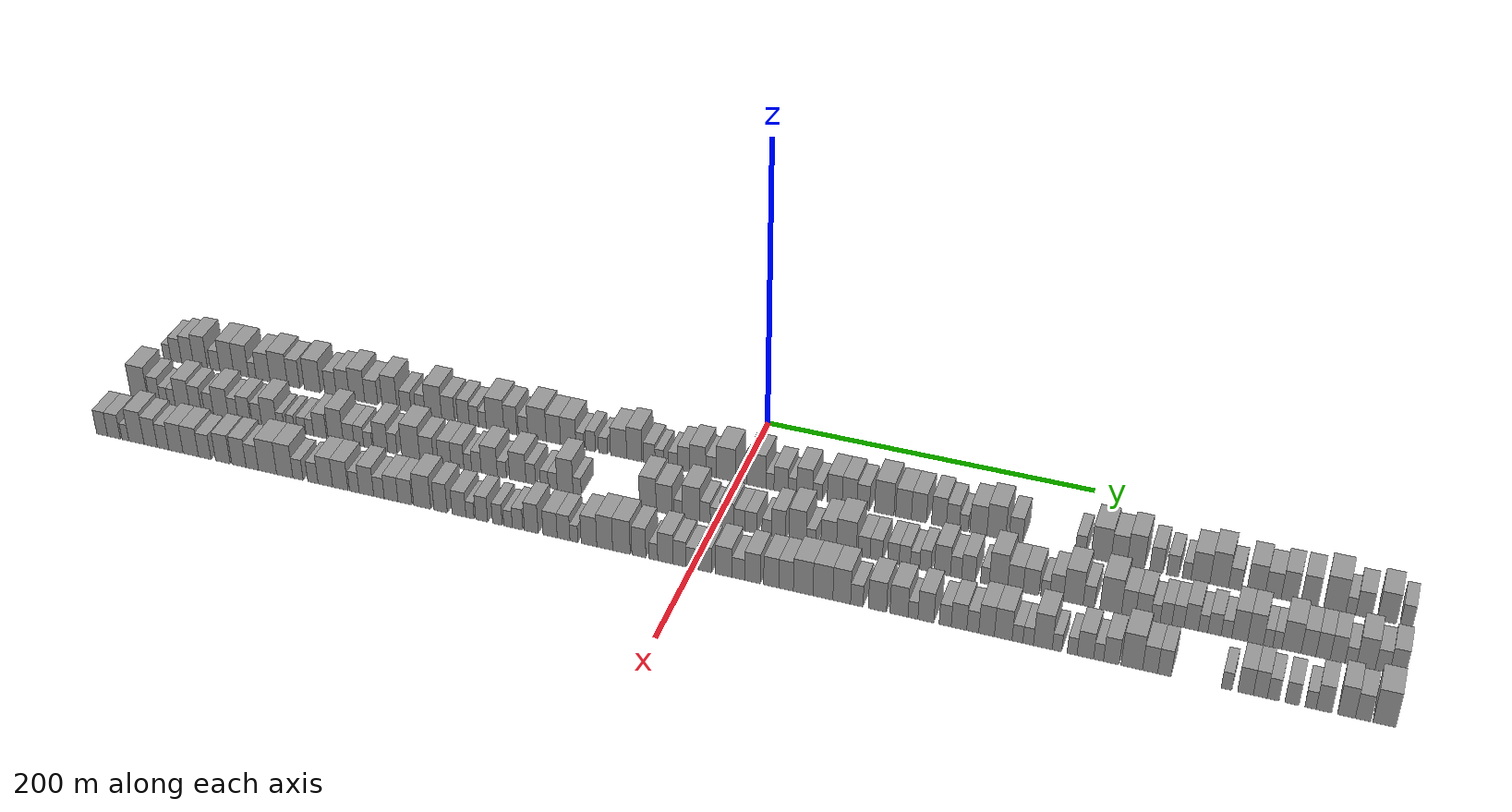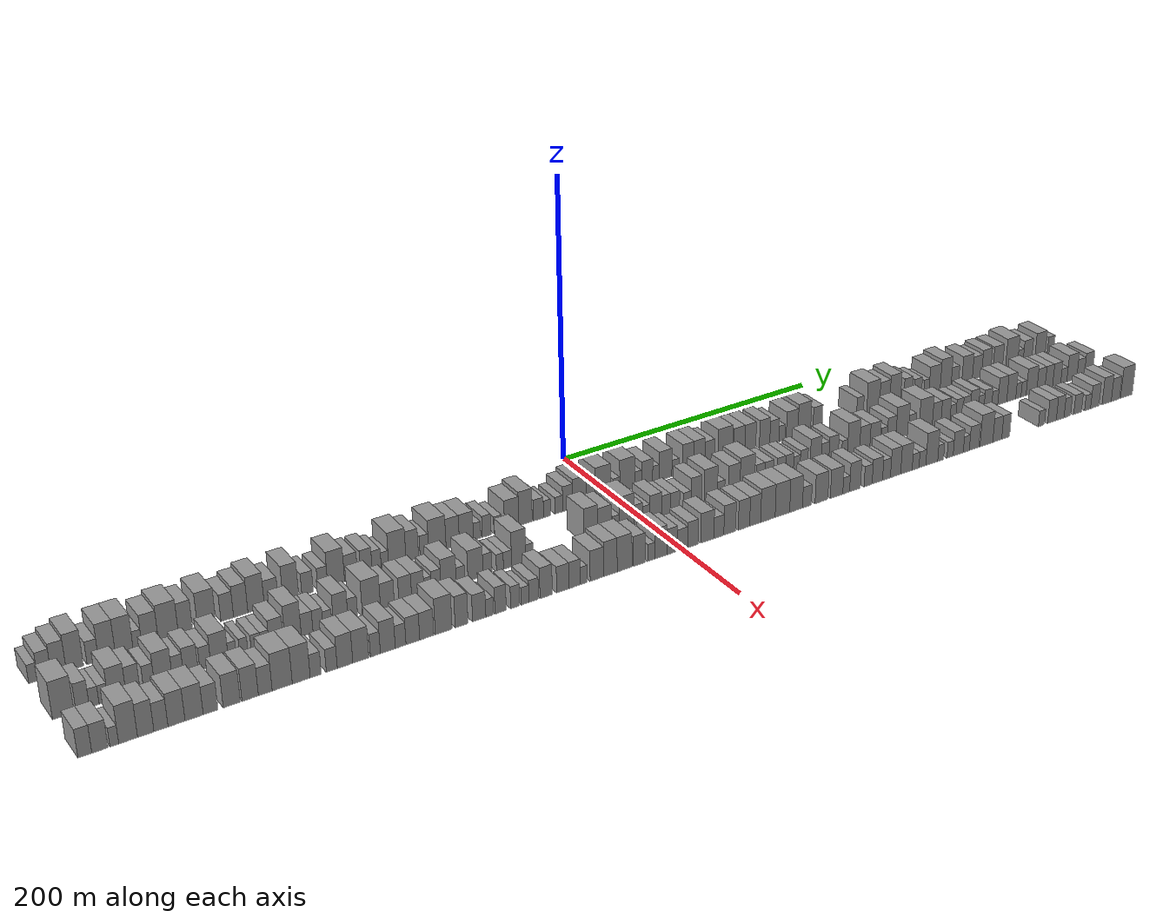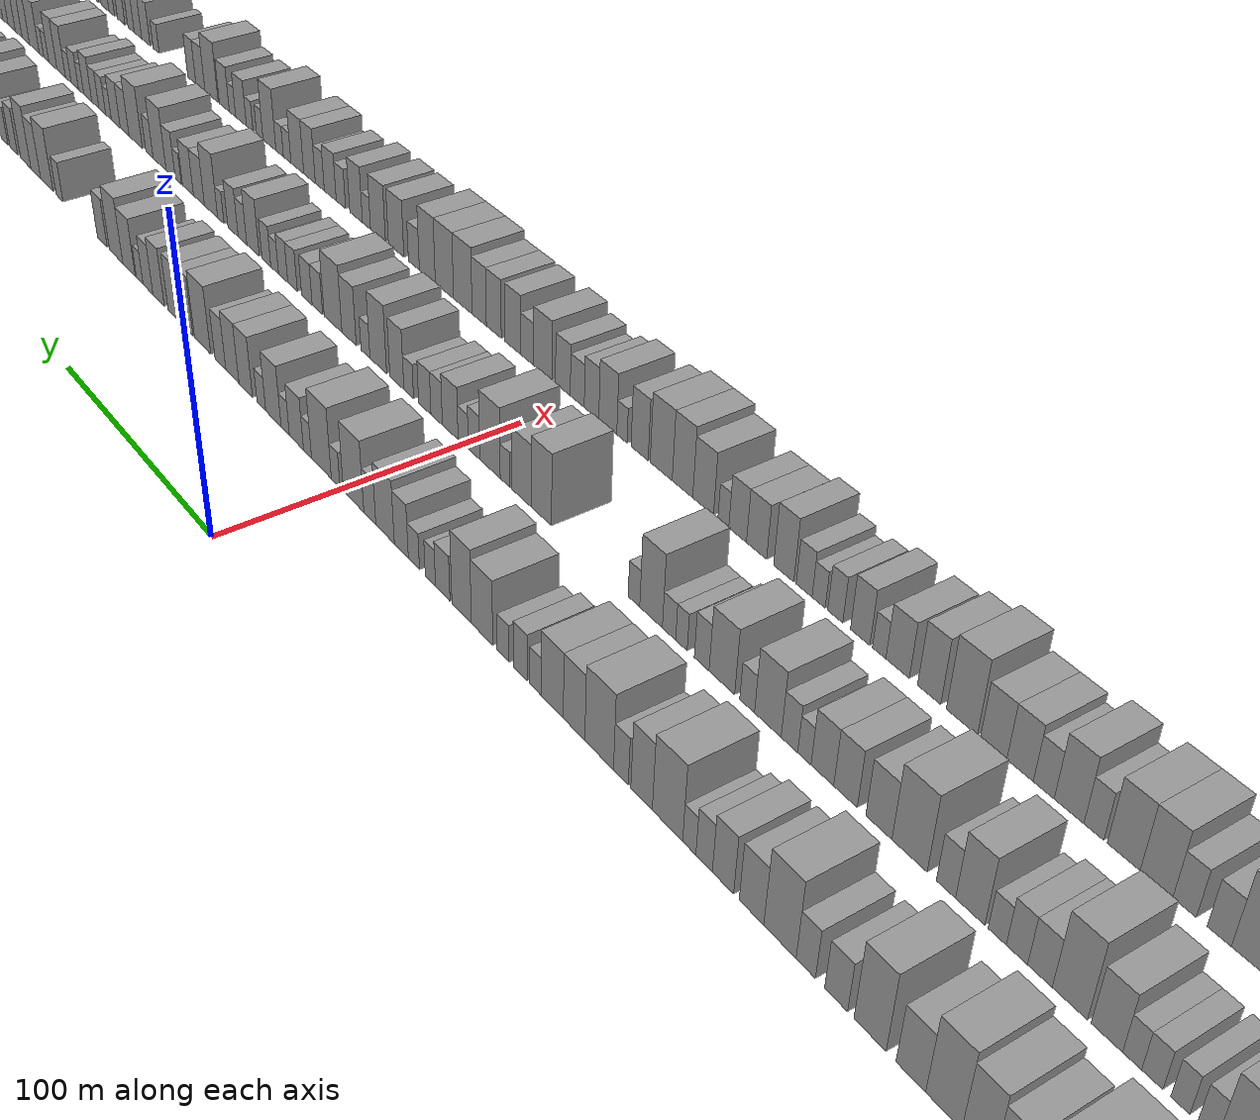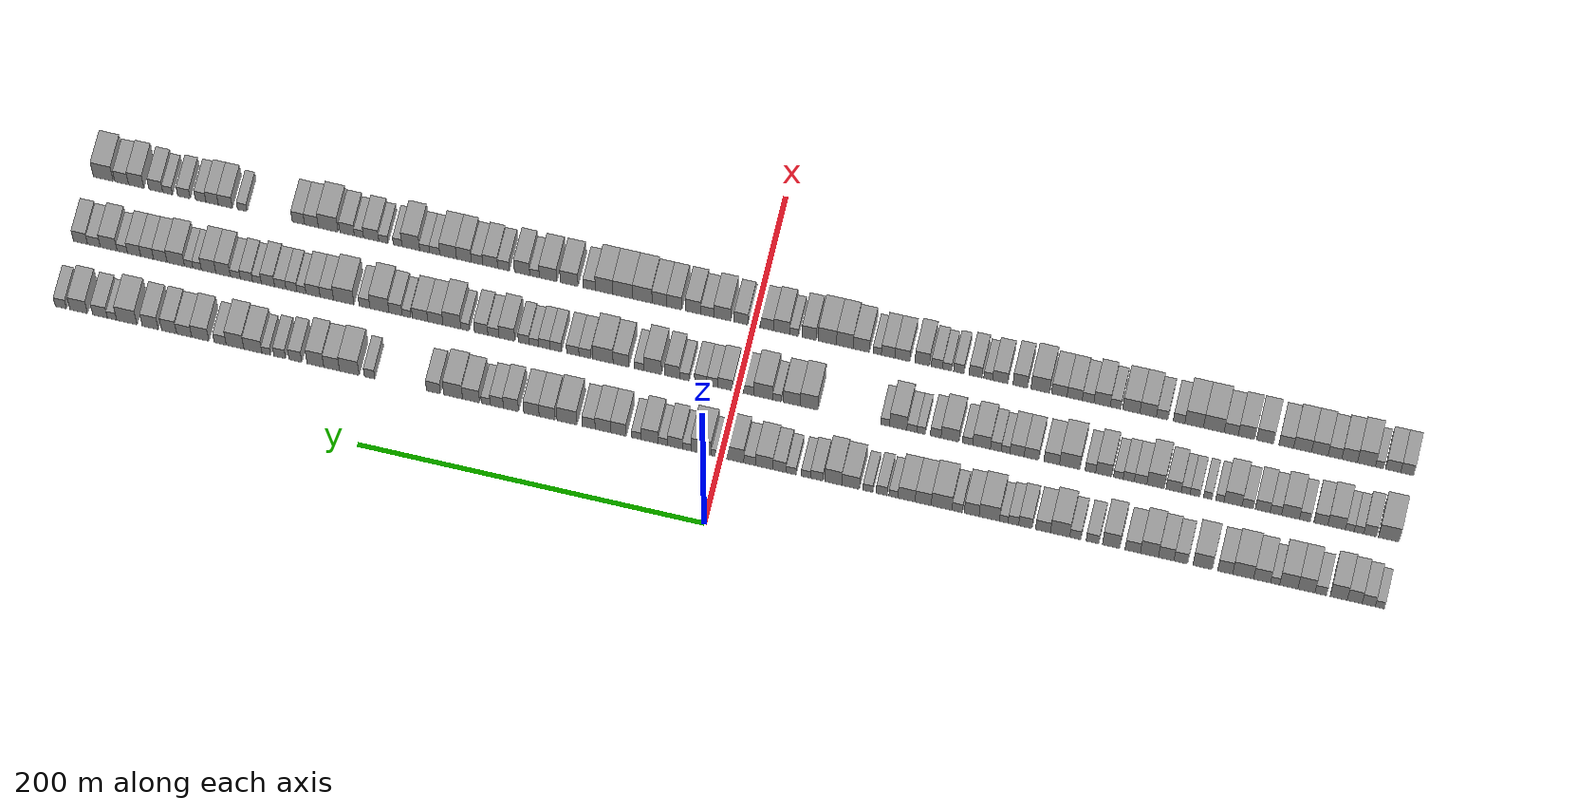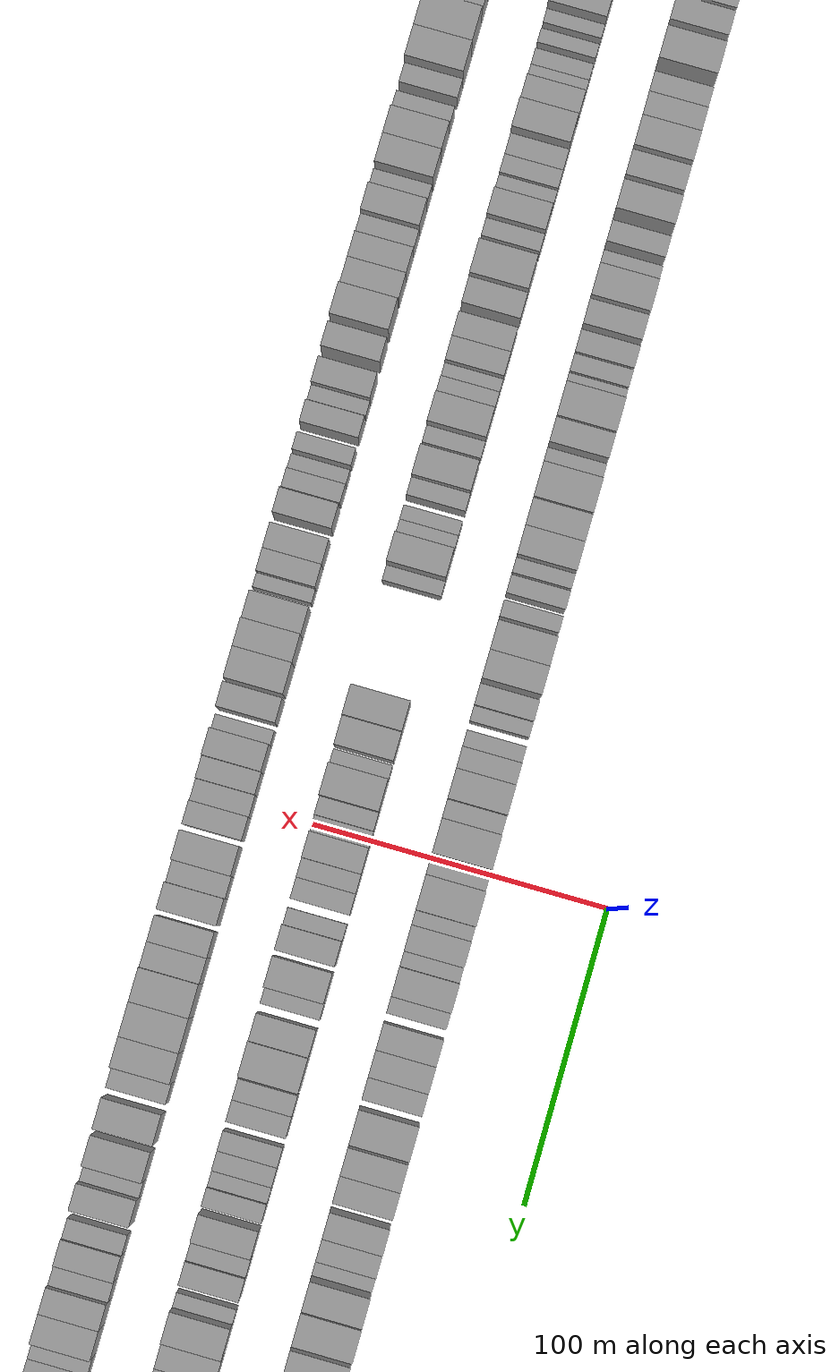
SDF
<sdf version="1.6">
 <world name="default">
  <scene>
   <sky><clouds><speed>12</speed></clouds></sky>
   <ambient>0.4 0.4 0.4 1</ambient>
   <background>0.7 0.7 0.7 1</background>
   <shadows>1</shadows>
  </scene>
  <gravity>0 0 -9.8066</gravity>
  <magnetic_field>6e-06 2.3e-05 -4.2e-05</magnetic_field>
  <physics default="0" name="default_physics" type="ode">
   <ode>
    <solver>
     <type>quick</type>
     <iters>10</iters>
     <sor>1.0</sor>
     <use_dynamic_moi_rescaling>0</use_dynamic_moi_rescaling>
    </solver>
    <constraints>
     <cfm>0</cfm>
     <erp>0.2</erp>
     <contact_max_correcting_vel>100</contact_max_correcting_vel>
     <contact_surface_layer>0.001</contact_surface_layer>
    </constraints>
   </ode>
   <max_step_size>0.004</max_step_size>
   <real_time_factor>1</real_time_factor>
   <real_time_update_rate>250</real_time_update_rate>
  </physics>
  <light name="sun" type="directional">
   <pose>0 0 10 0 0 0</pose>
   <diffuse>0.8 0.8 0.8 1</diffuse>
   <specular>0.2 0.2 0.2 1</specular>
   <attenuation>
    <range>1000</range>
    <constant>0.9</constant>
    <linear>0.01</linear>
    <quadratic>0.001</quadratic>
   </attenuation>
   <direction>-0.5 0.1 -0.9</direction>
  </light>
  <model name="building_1">
   <static>1</static>
   <pose>50.0000 -377.3886 0 0.000000 0.000000 0.000000</pose>
   <link name="link">
    <pose>0 0 6.00 0 0 0</pose>
    <collision name="collision"><geometry><box><size>20.0000 5.2227 12.0000</size></box></geometry></collision>
    <visual name="visual">
     <cast_shadows>0</cast_shadows>
     <geometry><box><size>20.0000 5.2227 12.0000</size></box></geometry>
     <material>
      <script>
       <uri>model://grey_wall/materials/scripts</uri>
       <uri>model://grey_wall/materials/textures</uri>
       <name>vrc/grey_wall</name>
      </script>
     </material>
    </visual>
   </link>
  </model>
  <model name="building_2">
   <static>1</static>
   <pose>50.0000 -371.0098 0 0.000000 0.000000 0.000000</pose>
   <link name="link">
    <pose>0 0 9.00 0 0 0</pose>
    <collision name="collision"><geometry><box><size>20.0000 7.5350 18.0000</size></box></geometry></collision>
    <visual name="visual">
     <cast_shadows>0</cast_shadows>
     <geometry><box><size>20.0000 7.5350 18.0000</size></box></geometry>
     <material>
      <script>
       <uri>model://grey_wall/materials/scripts</uri>
       <uri>model://grey_wall/materials/textures</uri>
       <name>vrc/grey_wall</name>
      </script>
     </material>
    </visual>
   </link>
  </model>
  <model name="building_3">
   <static>1</static>
   <pose>50.0000 -363.0318 0 0.000000 0.000000 0.000000</pose>
   <link name="link">
    <pose>0 0 10.50 0 0 0</pose>
    <collision name="collision"><geometry><box><size>20.0000 8.4210 21.0000</size></box></geometry></collision>
    <visual name="visual">
     <cast_shadows>0</cast_shadows>
     <geometry><box><size>20.0000 8.4210 21.0000</size></box></geometry>
     <material>
      <script>
       <uri>model://grey_wall/materials/scripts</uri>
       <uri>model://grey_wall/materials/textures</uri>
       <name>vrc/grey_wall</name>
      </script>
     </material>
    </visual>
   </link>
  </model>
  <model name="building_4">
   <static>1</static>
   <pose>50.0000 -353.9402 0 0.000000 0.000000 0.000000</pose>
   <link name="link">
    <pose>0 0 12.00 0 0 0</pose>
    <collision name="collision"><geometry><box><size>20.0000 9.7621 24.0000</size></box></geometry></collision>
    <visual name="visual">
     <cast_shadows>0</cast_shadows>
     <geometry><box><size>20.0000 9.7621 24.0000</size></box></geometry>
     <material>
      <script>
       <uri>model://grey_wall/materials/scripts</uri>
       <uri>model://grey_wall/materials/textures</uri>
       <name>vrc/grey_wall</name>
      </script>
     </material>
    </visual>
   </link>
  </model>
  <model name="building_5">
   <static>1</static>
   <pose>50.0000 -343.7180 0 0.000000 0.000000 0.000000</pose>
   <link name="link">
    <pose>0 0 7.50 0 0 0</pose>
    <collision name="collision"><geometry><box><size>20.0000 6.6824 15.0000</size></box></geometry></collision>
    <visual name="visual">
     <cast_shadows>0</cast_shadows>
     <geometry><box><size>20.0000 6.6824 15.0000</size></box></geometry>
     <material>
      <script>
       <uri>model://grey_wall/materials/scripts</uri>
       <uri>model://grey_wall/materials/textures</uri>
       <name>vrc/grey_wall</name>
      </script>
     </material>
    </visual>
   </link>
  </model>
  <model name="building_6">
   <static>1</static>
   <pose>50.0000 -335.5096 0 0.000000 0.000000 0.000000</pose>
   <link name="link">
    <pose>0 0 12.00 0 0 0</pose>
    <collision name="collision"><geometry><box><size>20.0000 9.7343 24.0000</size></box></geometry></collision>
    <visual name="visual">
     <cast_shadows>0</cast_shadows>
     <geometry><box><size>20.0000 9.7343 24.0000</size></box></geometry>
     <material>
      <script>
       <uri>model://grey_wall/materials/scripts</uri>
       <uri>model://grey_wall/materials/textures</uri>
       <name>vrc/grey_wall</name>
      </script>
     </material>
    </visual>
   </link>
  </model>
  <model name="building_7">
   <static>1</static>
   <pose>50.0000 -325.4724 0 0.000000 0.000000 0.000000</pose>
   <link name="link">
    <pose>0 0 12.00 0 0 0</pose>
    <collision name="collision"><geometry><box><size>20.0000 10.3402 24.0000</size></box></geometry></collision>
    <visual name="visual">
     <cast_shadows>0</cast_shadows>
     <geometry><box><size>20.0000 10.3402 24.0000</size></box></geometry>
     <material>
      <script>
       <uri>model://grey_wall/materials/scripts</uri>
       <uri>model://grey_wall/materials/textures</uri>
       <name>vrc/grey_wall</name>
      </script>
     </material>
    </visual>
   </link>
  </model>
  <model name="building_8">
   <static>1</static>
   <pose>50.0000 -317.7057 0 0.000000 0.000000 0.000000</pose>
   <link name="link">
    <pose>0 0 6.00 0 0 0</pose>
    <collision name="collision"><geometry><box><size>20.0000 5.1933 12.0000</size></box></geometry></collision>
    <visual name="visual">
     <cast_shadows>0</cast_shadows>
     <geometry><box><size>20.0000 5.1933 12.0000</size></box></geometry>
     <material>
      <script>
       <uri>model://grey_wall/materials/scripts</uri>
       <uri>model://grey_wall/materials/textures</uri>
       <name>vrc/grey_wall</name>
      </script>
     </material>
    </visual>
   </link>
  </model>
  <model name="building_9">
   <static>1</static>
   <pose>50.0000 -310.2537 0 0.000000 0.000000 0.000000</pose>
   <link name="link">
    <pose>0 0 10.50 0 0 0</pose>
    <collision name="collision"><geometry><box><size>20.0000 9.7105 21.0000</size></box></geometry></collision>
    <visual name="visual">
     <cast_shadows>0</cast_shadows>
     <geometry><box><size>20.0000 9.7105 21.0000</size></box></geometry>
     <material>
      <script>
       <uri>model://grey_wall/materials/scripts</uri>
       <uri>model://grey_wall/materials/textures</uri>
       <name>vrc/grey_wall</name>
      </script>
     </material>
    </visual>
   </link>
  </model>
  <model name="building_10">
   <static>1</static>
   <pose>50.0000 -299.4055 0 0.000000 0.000000 0.000000</pose>
   <link name="link">
    <pose>0 0 12.00 0 0 0</pose>
    <collision name="collision"><geometry><box><size>20.0000 11.9860 24.0000</size></box></geometry></collision>
    <visual name="visual">
     <cast_shadows>0</cast_shadows>
     <geometry><box><size>20.0000 11.9860 24.0000</size></box></geometry>
     <material>
      <script>
       <uri>model://grey_wall/materials/scripts</uri>
       <uri>model://grey_wall/materials/textures</uri>
       <name>vrc/grey_wall</name>
      </script>
     </material>
    </visual>
   </link>
  </model>
  <model name="building_11">
   <static>1</static>
   <pose>50.0000 -289.1540 0 0.000000 0.000000 0.000000</pose>
   <link name="link">
    <pose>0 0 10.50 0 0 0</pose>
    <collision name="collision"><geometry><box><size>20.0000 8.5169 21.0000</size></box></geometry></collision>
    <visual name="visual">
     <cast_shadows>0</cast_shadows>
     <geometry><box><size>20.0000 8.5169 21.0000</size></box></geometry>
     <material>
      <script>
       <uri>model://grey_wall/materials/scripts</uri>
       <uri>model://grey_wall/materials/textures</uri>
       <name>vrc/grey_wall</name>
      </script>
     </material>
    </visual>
   </link>
  </model>
  <model name="building_12">
   <static>1</static>
   <pose>50.0000 -276.3157 0 0.000000 0.000000 0.000000</pose>
   <link name="link">
    <pose>0 0 12.00 0 0 0</pose>
    <collision name="collision"><geometry><box><size>20.0000 11.1597 24.0000</size></box></geometry></collision>
    <visual name="visual">
     <cast_shadows>0</cast_shadows>
     <geometry><box><size>20.0000 11.1597 24.0000</size></box></geometry>
     <material>
      <script>
       <uri>model://grey_wall/materials/scripts</uri>
       <uri>model://grey_wall/materials/textures</uri>
       <name>vrc/grey_wall</name>
      </script>
     </material>
    </visual>
   </link>
  </model>
  <model name="building_13">
   <static>1</static>
   <pose>50.0000 -263.8303 0 0.000000 0.000000 0.000000</pose>
   <link name="link">
    <pose>0 0 9.00 0 0 0</pose>
    <collision name="collision"><geometry><box><size>20.0000 7.8110 18.0000</size></box></geometry></collision>
    <visual name="visual">
     <cast_shadows>0</cast_shadows>
     <geometry><box><size>20.0000 7.8110 18.0000</size></box></geometry>
     <material>
      <script>
       <uri>model://grey_wall/materials/scripts</uri>
       <uri>model://grey_wall/materials/textures</uri>
       <name>vrc/grey_wall</name>
      </script>
     </material>
    </visual>
   </link>
  </model>
  <model name="building_14">
   <static>1</static>
   <pose>50.0000 -255.4769 0 0.000000 0.000000 0.000000</pose>
   <link name="link">
    <pose>0 0 10.50 0 0 0</pose>
    <collision name="collision"><geometry><box><size>20.0000 8.8958 21.0000</size></box></geometry></collision>
    <visual name="visual">
     <cast_shadows>0</cast_shadows>
     <geometry><box><size>20.0000 8.8958 21.0000</size></box></geometry>
     <material>
      <script>
       <uri>model://grey_wall/materials/scripts</uri>
       <uri>model://grey_wall/materials/textures</uri>
       <name>vrc/grey_wall</name>
      </script>
     </material>
    </visual>
   </link>
  </model>
  <model name="building_15">
   <static>1</static>
   <pose>50.0000 -245.8537 0 0.000000 0.000000 0.000000</pose>
   <link name="link">
    <pose>0 0 12.00 0 0 0</pose>
    <collision name="collision"><geometry><box><size>20.0000 10.3506 24.0000</size></box></geometry></collision>
    <visual name="visual">
     <cast_shadows>0</cast_shadows>
     <geometry><box><size>20.0000 10.3506 24.0000</size></box></geometry>
     <material>
      <script>
       <uri>model://grey_wall/materials/scripts</uri>
       <uri>model://grey_wall/materials/textures</uri>
       <name>vrc/grey_wall</name>
      </script>
     </material>
    </visual>
   </link>
  </model>
  <model name="building_16">
   <static>1</static>
   <pose>50.0000 -236.2907 0 0.000000 0.000000 0.000000</pose>
   <link name="link">
    <pose>0 0 9.00 0 0 0</pose>
    <collision name="collision"><geometry><box><size>20.0000 8.7754 18.0000</size></box></geometry></collision>
    <visual name="visual">
     <cast_shadows>0</cast_shadows>
     <geometry><box><size>20.0000 8.7754 18.0000</size></box></geometry>
     <material>
      <script>
       <uri>model://grey_wall/materials/scripts</uri>
       <uri>model://grey_wall/materials/textures</uri>
       <name>vrc/grey_wall</name>
      </script>
     </material>
    </visual>
   </link>
  </model>
  <model name="building_17">
   <static>1</static>
   <pose>50.0000 -223.9286 0 0.000000 0.000000 0.000000</pose>
   <link name="link">
    <pose>0 0 12.00 0 0 0</pose>
    <collision name="collision"><geometry><box><size>20.0000 9.9487 24.0000</size></box></geometry></collision>
    <visual name="visual">
     <cast_shadows>0</cast_shadows>
     <geometry><box><size>20.0000 9.9487 24.0000</size></box></geometry>
     <material>
      <script>
       <uri>model://grey_wall/materials/scripts</uri>
       <uri>model://grey_wall/materials/textures</uri>
       <name>vrc/grey_wall</name>
      </script>
     </material>
    </visual>
   </link>
  </model>
  <model name="building_18">
   <static>1</static>
   <pose>50.0000 -213.2876 0 0.000000 0.000000 0.000000</pose>
   <link name="link">
    <pose>0 0 7.50 0 0 0</pose>
    <collision name="collision"><geometry><box><size>20.0000 7.3333 15.0000</size></box></geometry></collision>
    <visual name="visual">
     <cast_shadows>0</cast_shadows>
     <geometry><box><size>20.0000 7.3333 15.0000</size></box></geometry>
     <material>
      <script>
       <uri>model://grey_wall/materials/scripts</uri>
       <uri>model://grey_wall/materials/textures</uri>
       <name>vrc/grey_wall</name>
      </script>
     </material>
    </visual>
   </link>
  </model>
  <model name="building_19">
   <static>1</static>
   <pose>50.0000 -203.4211 0 0.000000 0.000000 0.000000</pose>
   <link name="link">
    <pose>0 0 7.50 0 0 0</pose>
    <collision name="collision"><geometry><box><size>20.0000 6.3996 15.0000</size></box></geometry></collision>
    <visual name="visual">
     <cast_shadows>0</cast_shadows>
     <geometry><box><size>20.0000 6.3996 15.0000</size></box></geometry>
     <material>
      <script>
       <uri>model://grey_wall/materials/scripts</uri>
       <uri>model://grey_wall/materials/textures</uri>
       <name>vrc/grey_wall</name>
      </script>
     </material>
    </visual>
   </link>
  </model>
  <model name="building_20">
   <static>1</static>
   <pose>50.0000 -194.7316 0 0.000000 0.000000 0.000000</pose>
   <link name="link">
    <pose>0 0 12.00 0 0 0</pose>
    <collision name="collision"><geometry><box><size>20.0000 10.9794 24.0000</size></box></geometry></collision>
    <visual name="visual">
     <cast_shadows>0</cast_shadows>
     <geometry><box><size>20.0000 10.9794 24.0000</size></box></geometry>
     <material>
      <script>
       <uri>model://grey_wall/materials/scripts</uri>
       <uri>model://grey_wall/materials/textures</uri>
       <name>vrc/grey_wall</name>
      </script>
     </material>
    </visual>
   </link>
  </model>
  <model name="building_21">
   <static>1</static>
   <pose>50.0000 -184.9429 0 0.000000 0.000000 0.000000</pose>
   <link name="link">
    <pose>0 0 9.00 0 0 0</pose>
    <collision name="collision"><geometry><box><size>20.0000 8.5980 18.0000</size></box></geometry></collision>
    <visual name="visual">
     <cast_shadows>0</cast_shadows>
     <geometry><box><size>20.0000 8.5980 18.0000</size></box></geometry>
     <material>
      <script>
       <uri>model://grey_wall/materials/scripts</uri>
       <uri>model://grey_wall/materials/textures</uri>
       <name>vrc/grey_wall</name>
      </script>
     </material>
    </visual>
   </link>
  </model>
  <model name="building_22">
   <static>1</static>
   <pose>50.0000 -174.7971 0 0.000000 0.000000 0.000000</pose>
   <link name="link">
    <pose>0 0 9.00 0 0 0</pose>
    <collision name="collision"><geometry><box><size>20.0000 7.6934 18.0000</size></box></geometry></collision>
    <visual name="visual">
     <cast_shadows>0</cast_shadows>
     <geometry><box><size>20.0000 7.6934 18.0000</size></box></geometry>
     <material>
      <script>
       <uri>model://grey_wall/materials/scripts</uri>
       <uri>model://grey_wall/materials/textures</uri>
       <name>vrc/grey_wall</name>
      </script>
     </material>
    </visual>
   </link>
  </model>
  <model name="building_23">
   <static>1</static>
   <pose>50.0000 -167.9164 0 0.000000 0.000000 0.000000</pose>
   <link name="link">
    <pose>0 0 7.50 0 0 0</pose>
    <collision name="collision"><geometry><box><size>20.0000 6.0680 15.0000</size></box></geometry></collision>
    <visual name="visual">
     <cast_shadows>0</cast_shadows>
     <geometry><box><size>20.0000 6.0680 15.0000</size></box></geometry>
     <material>
      <script>
       <uri>model://grey_wall/materials/scripts</uri>
       <uri>model://grey_wall/materials/textures</uri>
       <name>vrc/grey_wall</name>
      </script>
     </material>
    </visual>
   </link>
  </model>
  <model name="building_24">
   <static>1</static>
   <pose>50.0000 -162.3977 0 0.000000 0.000000 0.000000</pose>
   <link name="link">
    <pose>0 0 6.00 0 0 0</pose>
    <collision name="collision"><geometry><box><size>20.0000 4.9694 12.0000</size></box></geometry></collision>
    <visual name="visual">
     <cast_shadows>0</cast_shadows>
     <geometry><box><size>20.0000 4.9694 12.0000</size></box></geometry>
     <material>
      <script>
       <uri>model://grey_wall/materials/scripts</uri>
       <uri>model://grey_wall/materials/textures</uri>
       <name>vrc/grey_wall</name>
      </script>
     </material>
    </visual>
   </link>
  </model>
  <model name="building_25">
   <static>1</static>
   <pose>50.0000 -154.0770 0 0.000000 0.000000 0.000000</pose>
   <link name="link">
    <pose>0 0 12.00 0 0 0</pose>
    <collision name="collision"><geometry><box><size>20.0000 11.6722 24.0000</size></box></geometry></collision>
    <visual name="visual">
     <cast_shadows>0</cast_shadows>
     <geometry><box><size>20.0000 11.6722 24.0000</size></box></geometry>
     <material>
      <script>
       <uri>model://grey_wall/materials/scripts</uri>
       <uri>model://grey_wall/materials/textures</uri>
       <name>vrc/grey_wall</name>
      </script>
     </material>
    </visual>
   </link>
  </model>
  <model name="building_26">
   <static>1</static>
   <pose>50.0000 -143.9852 0 0.000000 0.000000 0.000000</pose>
   <link name="link">
    <pose>0 0 10.50 0 0 0</pose>
    <collision name="collision"><geometry><box><size>20.0000 8.5114 21.0000</size></box></geometry></collision>
    <visual name="visual">
     <cast_shadows>0</cast_shadows>
     <geometry><box><size>20.0000 8.5114 21.0000</size></box></geometry>
     <material>
      <script>
       <uri>model://grey_wall/materials/scripts</uri>
       <uri>model://grey_wall/materials/textures</uri>
       <name>vrc/grey_wall</name>
      </script>
     </material>
    </visual>
   </link>
  </model>
  <model name="building_27">
   <static>1</static>
   <pose>50.0000 -135.7259 0 0.000000 0.000000 0.000000</pose>
   <link name="link">
    <pose>0 0 7.50 0 0 0</pose>
    <collision name="collision"><geometry><box><size>20.0000 6.0072 15.0000</size></box></geometry></collision>
    <visual name="visual">
     <cast_shadows>0</cast_shadows>
     <geometry><box><size>20.0000 6.0072 15.0000</size></box></geometry>
     <material>
      <script>
       <uri>model://grey_wall/materials/scripts</uri>
       <uri>model://grey_wall/materials/textures</uri>
       <name>vrc/grey_wall</name>
      </script>
     </material>
    </visual>
   </link>
  </model>
  <model name="building_28">
   <static>1</static>
   <pose>50.0000 -126.7487 0 0.000000 0.000000 0.000000</pose>
   <link name="link">
    <pose>0 0 12.00 0 0 0</pose>
    <collision name="collision"><geometry><box><size>20.0000 11.9471 24.0000</size></box></geometry></collision>
    <visual name="visual">
     <cast_shadows>0</cast_shadows>
     <geometry><box><size>20.0000 11.9471 24.0000</size></box></geometry>
     <material>
      <script>
       <uri>model://grey_wall/materials/scripts</uri>
       <uri>model://grey_wall/materials/textures</uri>
       <name>vrc/grey_wall</name>
      </script>
     </material>
    </visual>
   </link>
  </model>
  <model name="building_29">
   <static>1</static>
   <pose>50.0000 -116.1441 0 0.000000 0.000000 0.000000</pose>
   <link name="link">
    <pose>0 0 10.50 0 0 0</pose>
    <collision name="collision"><geometry><box><size>20.0000 9.2621 21.0000</size></box></geometry></collision>
    <visual name="visual">
     <cast_shadows>0</cast_shadows>
     <geometry><box><size>20.0000 9.2621 21.0000</size></box></geometry>
     <material>
      <script>
       <uri>model://grey_wall/materials/scripts</uri>
       <uri>model://grey_wall/materials/textures</uri>
       <name>vrc/grey_wall</name>
      </script>
     </material>
    </visual>
   </link>
  </model>
  <model name="building_30">
   <static>1</static>
   <pose>50.0000 -106.5851 0 0.000000 0.000000 0.000000</pose>
   <link name="link">
    <pose>0 0 10.50 0 0 0</pose>
    <collision name="collision"><geometry><box><size>20.0000 9.8558 21.0000</size></box></geometry></collision>
    <visual name="visual">
     <cast_shadows>0</cast_shadows>
     <geometry><box><size>20.0000 9.8558 21.0000</size></box></geometry>
     <material>
      <script>
       <uri>model://grey_wall/materials/scripts</uri>
       <uri>model://grey_wall/materials/textures</uri>
       <name>vrc/grey_wall</name>
      </script>
     </material>
    </visual>
   </link>
  </model>
  <model name="building_31">
   <static>1</static>
   <pose>50.0000 -99.0614 0 0.000000 0.000000 0.000000</pose>
   <link name="link">
    <pose>0 0 6.00 0 0 0</pose>
    <collision name="collision"><geometry><box><size>20.0000 5.1916 12.0000</size></box></geometry></collision>
    <visual name="visual">
     <cast_shadows>0</cast_shadows>
     <geometry><box><size>20.0000 5.1916 12.0000</size></box></geometry>
     <material>
      <script>
       <uri>model://grey_wall/materials/scripts</uri>
       <uri>model://grey_wall/materials/textures</uri>
       <name>vrc/grey_wall</name>
      </script>
     </material>
    </visual>
   </link>
  </model>
  <model name="building_32">
   <static>1</static>
   <pose>50.0000 -92.3239 0 0.000000 0.000000 0.000000</pose>
   <link name="link">
    <pose>0 0 7.50 0 0 0</pose>
    <collision name="collision"><geometry><box><size>20.0000 6.2834 15.0000</size></box></geometry></collision>
    <visual name="visual">
     <cast_shadows>0</cast_shadows>
     <geometry><box><size>20.0000 6.2834 15.0000</size></box></geometry>
     <material>
      <script>
       <uri>model://grey_wall/materials/scripts</uri>
       <uri>model://grey_wall/materials/textures</uri>
       <name>vrc/grey_wall</name>
      </script>
     </material>
    </visual>
   </link>
  </model>
  <model name="building_33">
   <static>1</static>
   <pose>50.0000 -84.3592 0 0.000000 0.000000 0.000000</pose>
   <link name="link">
    <pose>0 0 6.00 0 0 0</pose>
    <collision name="collision"><geometry><box><size>20.0000 5.6460 12.0000</size></box></geometry></collision>
    <visual name="visual">
     <cast_shadows>0</cast_shadows>
     <geometry><box><size>20.0000 5.6460 12.0000</size></box></geometry>
     <material>
      <script>
       <uri>model://grey_wall/materials/scripts</uri>
       <uri>model://grey_wall/materials/textures</uri>
       <name>vrc/grey_wall</name>
      </script>
     </material>
    </visual>
   </link>
  </model>
  <model name="building_34">
   <static>1</static>
   <pose>50.0000 -74.3983 0 0.000000 0.000000 0.000000</pose>
   <link name="link">
    <pose>0 0 10.50 0 0 0</pose>
    <collision name="collision"><geometry><box><size>20.0000 10.2758 21.0000</size></box></geometry></collision>
    <visual name="visual">
     <cast_shadows>0</cast_shadows>
     <geometry><box><size>20.0000 10.2758 21.0000</size></box></geometry>
     <material>
      <script>
       <uri>model://grey_wall/materials/scripts</uri>
       <uri>model://grey_wall/materials/textures</uri>
       <name>vrc/grey_wall</name>
      </script>
     </material>
    </visual>
   </link>
  </model>
  <model name="building_35">
   <static>1</static>
   <pose>50.0000 -64.4441 0 0.000000 0.000000 0.000000</pose>
   <link name="link">
    <pose>0 0 12.00 0 0 0</pose>
    <collision name="collision"><geometry><box><size>20.0000 9.6326 24.0000</size></box></geometry></collision>
    <visual name="visual">
     <cast_shadows>0</cast_shadows>
     <geometry><box><size>20.0000 9.6326 24.0000</size></box></geometry>
     <material>
      <script>
       <uri>model://grey_wall/materials/scripts</uri>
       <uri>model://grey_wall/materials/textures</uri>
       <name>vrc/grey_wall</name>
      </script>
     </material>
    </visual>
   </link>
  </model>
  <model name="building_36">
   <static>1</static>
   <pose>50.0000 -54.9744 0 0.000000 0.000000 0.000000</pose>
   <link name="link">
    <pose>0 0 7.50 0 0 0</pose>
    <collision name="collision"><geometry><box><size>20.0000 7.3068 15.0000</size></box></geometry></collision>
    <visual name="visual">
     <cast_shadows>0</cast_shadows>
     <geometry><box><size>20.0000 7.3068 15.0000</size></box></geometry>
     <material>
      <script>
       <uri>model://grey_wall/materials/scripts</uri>
       <uri>model://grey_wall/materials/textures</uri>
       <name>vrc/grey_wall</name>
      </script>
     </material>
    </visual>
   </link>
  </model>
  <model name="building_37">
   <static>1</static>
   <pose>50.0000 -48.6844 0 0.000000 0.000000 0.000000</pose>
   <link name="link">
    <pose>0 0 6.00 0 0 0</pose>
    <collision name="collision"><geometry><box><size>20.0000 5.2732 12.0000</size></box></geometry></collision>
    <visual name="visual">
     <cast_shadows>0</cast_shadows>
     <geometry><box><size>20.0000 5.2732 12.0000</size></box></geometry>
     <material>
      <script>
       <uri>model://grey_wall/materials/scripts</uri>
       <uri>model://grey_wall/materials/textures</uri>
       <name>vrc/grey_wall</name>
      </script>
     </material>
    </visual>
   </link>
  </model>
  <model name="building_38">
   <static>1</static>
   <pose>50.0000 -40.1259 0 0.000000 0.000000 0.000000</pose>
   <link name="link">
    <pose>0 0 6.00 0 0 0</pose>
    <collision name="collision"><geometry><box><size>20.0000 5.8437 12.0000</size></box></geometry></collision>
    <visual name="visual">
     <cast_shadows>0</cast_shadows>
     <geometry><box><size>20.0000 5.8437 12.0000</size></box></geometry>
     <material>
      <script>
       <uri>model://grey_wall/materials/scripts</uri>
       <uri>model://grey_wall/materials/textures</uri>
       <name>vrc/grey_wall</name>
      </script>
     </material>
    </visual>
   </link>
  </model>
  <model name="building_39">
   <static>1</static>
   <pose>50.0000 -33.4594 0 0.000000 0.000000 0.000000</pose>
   <link name="link">
    <pose>0 0 9.00 0 0 0</pose>
    <collision name="collision"><geometry><box><size>20.0000 7.4892 18.0000</size></box></geometry></collision>
    <visual name="visual">
     <cast_shadows>0</cast_shadows>
     <geometry><box><size>20.0000 7.4892 18.0000</size></box></geometry>
     <material>
      <script>
       <uri>model://grey_wall/materials/scripts</uri>
       <uri>model://grey_wall/materials/textures</uri>
       <name>vrc/grey_wall</name>
      </script>
     </material>
    </visual>
   </link>
  </model>
  <model name="building_40">
   <static>1</static>
   <pose>50.0000 -24.6484 0 0.000000 0.000000 0.000000</pose>
   <link name="link">
    <pose>0 0 10.50 0 0 0</pose>
    <collision name="collision"><geometry><box><size>20.0000 10.1328 21.0000</size></box></geometry></collision>
    <visual name="visual">
     <cast_shadows>0</cast_shadows>
     <geometry><box><size>20.0000 10.1328 21.0000</size></box></geometry>
     <material>
      <script>
       <uri>model://grey_wall/materials/scripts</uri>
       <uri>model://grey_wall/materials/textures</uri>
       <name>vrc/grey_wall</name>
      </script>
     </material>
    </visual>
   </link>
  </model>
  <model name="building_41">
   <static>1</static>
   <pose>50.0000 -16.2429 0 0.000000 0.000000 0.000000</pose>
   <link name="link">
    <pose>0 0 7.50 0 0 0</pose>
    <collision name="collision"><geometry><box><size>20.0000 6.6781 15.0000</size></box></geometry></collision>
    <visual name="visual">
     <cast_shadows>0</cast_shadows>
     <geometry><box><size>20.0000 6.6781 15.0000</size></box></geometry>
     <material>
      <script>
       <uri>model://grey_wall/materials/scripts</uri>
       <uri>model://grey_wall/materials/textures</uri>
       <name>vrc/grey_wall</name>
      </script>
     </material>
    </visual>
   </link>
  </model>
  <model name="building_42">
   <static>1</static>
   <pose>50.0000 -7.0785 0 0.000000 0.000000 0.000000</pose>
   <link name="link">
    <pose>0 0 12.00 0 0 0</pose>
    <collision name="collision"><geometry><box><size>20.0000 11.6508 24.0000</size></box></geometry></collision>
    <visual name="visual">
     <cast_shadows>0</cast_shadows>
     <geometry><box><size>20.0000 11.6508 24.0000</size></box></geometry>
     <material>
      <script>
       <uri>model://grey_wall/materials/scripts</uri>
       <uri>model://grey_wall/materials/textures</uri>
       <name>vrc/grey_wall</name>
      </script>
     </material>
    </visual>
   </link>
  </model>
  <model name="building_43">
   <static>1</static>
   <pose>50.0000 3.2836 0 0.000000 0.000000 0.000000</pose>
   <link name="link">
    <pose>0 0 6.00 0 0 0</pose>
    <collision name="collision"><geometry><box><size>20.0000 5.0733 12.0000</size></box></geometry></collision>
    <visual name="visual">
     <cast_shadows>0</cast_shadows>
     <geometry><box><size>20.0000 5.0733 12.0000</size></box></geometry>
     <material>
      <script>
       <uri>model://grey_wall/materials/scripts</uri>
       <uri>model://grey_wall/materials/textures</uri>
       <name>vrc/grey_wall</name>
      </script>
     </material>
    </visual>
   </link>
  </model>
  <model name="building_44">
   <static>1</static>
   <pose>50.0000 11.7085 0 0.000000 0.000000 0.000000</pose>
   <link name="link">
    <pose>0 0 12.00 0 0 0</pose>
    <collision name="collision"><geometry><box><size>20.0000 11.7766 24.0000</size></box></geometry></collision>
    <visual name="visual">
     <cast_shadows>0</cast_shadows>
     <geometry><box><size>20.0000 11.7766 24.0000</size></box></geometry>
     <material>
      <script>
       <uri>model://grey_wall/materials/scripts</uri>
       <uri>model://grey_wall/materials/textures</uri>
       <name>vrc/grey_wall</name>
      </script>
     </material>
    </visual>
   </link>
  </model>
  <model name="building_45">
   <static>1</static>
   <pose>50.0000 20.0505 0 0.000000 0.000000 0.000000</pose>
   <link name="link">
    <pose>0 0 6.00 0 0 0</pose>
    <collision name="collision"><geometry><box><size>20.0000 4.9074 12.0000</size></box></geometry></collision>
    <visual name="visual">
     <cast_shadows>0</cast_shadows>
     <geometry><box><size>20.0000 4.9074 12.0000</size></box></geometry>
     <material>
      <script>
       <uri>model://grey_wall/materials/scripts</uri>
       <uri>model://grey_wall/materials/textures</uri>
       <name>vrc/grey_wall</name>
      </script>
     </material>
    </visual>
   </link>
  </model>
  <model name="building_46">
   <static>1</static>
   <pose>50.0000 26.8823 0 0.000000 0.000000 0.000000</pose>
   <link name="link">
    <pose>0 0 9.00 0 0 0</pose>
    <collision name="collision"><geometry><box><size>20.0000 8.7563 18.0000</size></box></geometry></collision>
    <visual name="visual">
     <cast_shadows>0</cast_shadows>
     <geometry><box><size>20.0000 8.7563 18.0000</size></box></geometry>
     <material>
      <script>
       <uri>model://grey_wall/materials/scripts</uri>
       <uri>model://grey_wall/materials/textures</uri>
       <name>vrc/grey_wall</name>
      </script>
     </material>
    </visual>
   </link>
  </model>
  <model name="building_47">
   <static>1</static>
   <pose>50.0000 33.8494 0 0.000000 0.000000 0.000000</pose>
   <link name="link">
    <pose>0 0 6.00 0 0 0</pose>
    <collision name="collision"><geometry><box><size>20.0000 5.1778 12.0000</size></box></geometry></collision>
    <visual name="visual">
     <cast_shadows>0</cast_shadows>
     <geometry><box><size>20.0000 5.1778 12.0000</size></box></geometry>
     <material>
      <script>
       <uri>model://grey_wall/materials/scripts</uri>
       <uri>model://grey_wall/materials/textures</uri>
       <name>vrc/grey_wall</name>
      </script>
     </material>
    </visual>
   </link>
  </model>
  <model name="building_48">
   <static>1</static>
   <pose>50.0000 41.3604 0 0.000000 0.000000 0.000000</pose>
   <link name="link">
    <pose>0 0 10.50 0 0 0</pose>
    <collision name="collision"><geometry><box><size>20.0000 9.8442 21.0000</size></box></geometry></collision>
    <visual name="visual">
     <cast_shadows>0</cast_shadows>
     <geometry><box><size>20.0000 9.8442 21.0000</size></box></geometry>
     <material>
      <script>
       <uri>model://grey_wall/materials/scripts</uri>
       <uri>model://grey_wall/materials/textures</uri>
       <name>vrc/grey_wall</name>
      </script>
     </material>
    </visual>
   </link>
  </model>
  <model name="building_49">
   <static>1</static>
   <pose>50.0000 49.1324 0 0.000000 0.000000 0.000000</pose>
   <link name="link">
    <pose>0 0 6.00 0 0 0</pose>
    <collision name="collision"><geometry><box><size>20.0000 5.6998 12.0000</size></box></geometry></collision>
    <visual name="visual">
     <cast_shadows>0</cast_shadows>
     <geometry><box><size>20.0000 5.6998 12.0000</size></box></geometry>
     <material>
      <script>
       <uri>model://grey_wall/materials/scripts</uri>
       <uri>model://grey_wall/materials/textures</uri>
       <name>vrc/grey_wall</name>
      </script>
     </material>
    </visual>
   </link>
  </model>
  <model name="building_50">
   <static>1</static>
   <pose>50.0000 59.4849 0 0.000000 0.000000 0.000000</pose>
   <link name="link">
    <pose>0 0 10.50 0 0 0</pose>
    <collision name="collision"><geometry><box><size>20.0000 9.0052 21.0000</size></box></geometry></collision>
    <visual name="visual">
     <cast_shadows>0</cast_shadows>
     <geometry><box><size>20.0000 9.0052 21.0000</size></box></geometry>
     <material>
      <script>
       <uri>model://grey_wall/materials/scripts</uri>
       <uri>model://grey_wall/materials/textures</uri>
       <name>vrc/grey_wall</name>
      </script>
     </material>
    </visual>
   </link>
  </model>
  <model name="building_51">
   <static>1</static>
   <pose>50.0000 68.4617 0 0.000000 0.000000 0.000000</pose>
   <link name="link">
    <pose>0 0 10.50 0 0 0</pose>
    <collision name="collision"><geometry><box><size>20.0000 8.9484 21.0000</size></box></geometry></collision>
    <visual name="visual">
     <cast_shadows>0</cast_shadows>
     <geometry><box><size>20.0000 8.9484 21.0000</size></box></geometry>
     <material>
      <script>
       <uri>model://grey_wall/materials/scripts</uri>
       <uri>model://grey_wall/materials/textures</uri>
       <name>vrc/grey_wall</name>
      </script>
     </material>
    </visual>
   </link>
  </model>
  <model name="building_52">
   <static>1</static>
   <pose>50.0000 76.6912 0 0.000000 0.000000 0.000000</pose>
   <link name="link">
    <pose>0 0 9.00 0 0 0</pose>
    <collision name="collision"><geometry><box><size>20.0000 7.5105 18.0000</size></box></geometry></collision>
    <visual name="visual">
     <cast_shadows>0</cast_shadows>
     <geometry><box><size>20.0000 7.5105 18.0000</size></box></geometry>
     <material>
      <script>
       <uri>model://grey_wall/materials/scripts</uri>
       <uri>model://grey_wall/materials/textures</uri>
       <name>vrc/grey_wall</name>
      </script>
     </material>
    </visual>
   </link>
  </model>
  <model name="building_53">
   <static>1</static>
   <pose>50.0000 89.2571 0 0.000000 0.000000 0.000000</pose>
   <link name="link">
    <pose>0 0 12.00 0 0 0</pose>
    <collision name="collision"><geometry><box><size>20.0000 11.6213 24.0000</size></box></geometry></collision>
    <visual name="visual">
     <cast_shadows>0</cast_shadows>
     <geometry><box><size>20.0000 11.6213 24.0000</size></box></geometry>
     <material>
      <script>
       <uri>model://grey_wall/materials/scripts</uri>
       <uri>model://grey_wall/materials/textures</uri>
       <name>vrc/grey_wall</name>
      </script>
     </material>
    </visual>
   </link>
  </model>
  <model name="building_54">
   <static>1</static>
   <pose>50.0000 100.7231 0 0.000000 0.000000 0.000000</pose>
   <link name="link">
    <pose>0 0 10.50 0 0 0</pose>
    <collision name="collision"><geometry><box><size>20.0000 9.3108 21.0000</size></box></geometry></collision>
    <visual name="visual">
     <cast_shadows>0</cast_shadows>
     <geometry><box><size>20.0000 9.3108 21.0000</size></box></geometry>
     <material>
      <script>
       <uri>model://grey_wall/materials/scripts</uri>
       <uri>model://grey_wall/materials/textures</uri>
       <name>vrc/grey_wall</name>
      </script>
     </material>
    </visual>
   </link>
  </model>
  <model name="building_55">
   <static>1</static>
   <pose>50.0000 109.8539 0 0.000000 0.000000 0.000000</pose>
   <link name="link">
    <pose>0 0 10.50 0 0 0</pose>
    <collision name="collision"><geometry><box><size>20.0000 8.9509 21.0000</size></box></geometry></collision>
    <visual name="visual">
     <cast_shadows>0</cast_shadows>
     <geometry><box><size>20.0000 8.9509 21.0000</size></box></geometry>
     <material>
      <script>
       <uri>model://grey_wall/materials/scripts</uri>
       <uri>model://grey_wall/materials/textures</uri>
       <name>vrc/grey_wall</name>
      </script>
     </material>
    </visual>
   </link>
  </model>
  <model name="building_56">
   <static>1</static>
   <pose>50.0000 121.6870 0 0.000000 0.000000 0.000000</pose>
   <link name="link">
    <pose>0 0 10.50 0 0 0</pose>
    <collision name="collision"><geometry><box><size>20.0000 8.7154 21.0000</size></box></geometry></collision>
    <visual name="visual">
     <cast_shadows>0</cast_shadows>
     <geometry><box><size>20.0000 8.7154 21.0000</size></box></geometry>
     <material>
      <script>
       <uri>model://grey_wall/materials/scripts</uri>
       <uri>model://grey_wall/materials/textures</uri>
       <name>vrc/grey_wall</name>
      </script>
     </material>
    </visual>
   </link>
  </model>
  <model name="building_57">
   <static>1</static>
   <pose>50.0000 129.8786 0 0.000000 0.000000 0.000000</pose>
   <link name="link">
    <pose>0 0 9.00 0 0 0</pose>
    <collision name="collision"><geometry><box><size>20.0000 7.6677 18.0000</size></box></geometry></collision>
    <visual name="visual">
     <cast_shadows>0</cast_shadows>
     <geometry><box><size>20.0000 7.6677 18.0000</size></box></geometry>
     <material>
      <script>
       <uri>model://grey_wall/materials/scripts</uri>
       <uri>model://grey_wall/materials/textures</uri>
       <name>vrc/grey_wall</name>
      </script>
     </material>
    </visual>
   </link>
  </model>
  <model name="building_58">
   <static>1</static>
   <pose>50.0000 136.3000 0 0.000000 0.000000 0.000000</pose>
   <link name="link">
    <pose>0 0 6.00 0 0 0</pose>
    <collision name="collision"><geometry><box><size>20.0000 5.1751 12.0000</size></box></geometry></collision>
    <visual name="visual">
     <cast_shadows>0</cast_shadows>
     <geometry><box><size>20.0000 5.1751 12.0000</size></box></geometry>
     <material>
      <script>
       <uri>model://grey_wall/materials/scripts</uri>
       <uri>model://grey_wall/materials/textures</uri>
       <name>vrc/grey_wall</name>
      </script>
     </material>
    </visual>
   </link>
  </model>
  <model name="building_59">
   <static>1</static>
   <pose>50.0000 144.8464 0 0.000000 0.000000 0.000000</pose>
   <link name="link">
    <pose>0 0 10.50 0 0 0</pose>
    <collision name="collision"><geometry><box><size>20.0000 9.9177 21.0000</size></box></geometry></collision>
    <visual name="visual">
     <cast_shadows>0</cast_shadows>
     <geometry><box><size>20.0000 9.9177 21.0000</size></box></geometry>
     <material>
      <script>
       <uri>model://grey_wall/materials/scripts</uri>
       <uri>model://grey_wall/materials/textures</uri>
       <name>vrc/grey_wall</name>
      </script>
     </material>
    </visual>
   </link>
  </model>
  <model name="building_60">
   <static>1</static>
   <pose>50.0000 155.2566 0 0.000000 0.000000 0.000000</pose>
   <link name="link">
    <pose>0 0 12.00 0 0 0</pose>
    <collision name="collision"><geometry><box><size>20.0000 10.9029 24.0000</size></box></geometry></collision>
    <visual name="visual">
     <cast_shadows>0</cast_shadows>
     <geometry><box><size>20.0000 10.9029 24.0000</size></box></geometry>
     <material>
      <script>
       <uri>model://grey_wall/materials/scripts</uri>
       <uri>model://grey_wall/materials/textures</uri>
       <name>vrc/grey_wall</name>
      </script>
     </material>
    </visual>
   </link>
  </model>
  <model name="building_61">
   <static>1</static>
   <pose>50.0000 166.7116 0 0.000000 0.000000 0.000000</pose>
   <link name="link">
    <pose>0 0 9.00 0 0 0</pose>
    <collision name="collision"><geometry><box><size>20.0000 8.0071 18.0000</size></box></geometry></collision>
    <visual name="visual">
     <cast_shadows>0</cast_shadows>
     <geometry><box><size>20.0000 8.0071 18.0000</size></box></geometry>
     <material>
      <script>
       <uri>model://grey_wall/materials/scripts</uri>
       <uri>model://grey_wall/materials/textures</uri>
       <name>vrc/grey_wall</name>
      </script>
     </material>
    </visual>
   </link>
  </model>
  <model name="building_62">
   <static>1</static>
   <pose>50.0000 203.7942 0 0.000000 0.000000 0.000000</pose>
   <link name="link">
    <pose>0 0 7.50 0 0 0</pose>
    <collision name="collision"><geometry><box><size>20.0000 6.0526 15.0000</size></box></geometry></collision>
    <visual name="visual">
     <cast_shadows>0</cast_shadows>
     <geometry><box><size>20.0000 6.0526 15.0000</size></box></geometry>
     <material>
      <script>
       <uri>model://grey_wall/materials/scripts</uri>
       <uri>model://grey_wall/materials/textures</uri>
       <name>vrc/grey_wall</name>
      </script>
     </material>
    </visual>
   </link>
  </model>
  <model name="building_63">
   <static>1</static>
   <pose>50.0000 215.5076 0 0.000000 0.000000 0.000000</pose>
   <link name="link">
    <pose>0 0 12.00 0 0 0</pose>
    <collision name="collision"><geometry><box><size>20.0000 11.3742 24.0000</size></box></geometry></collision>
    <visual name="visual">
     <cast_shadows>0</cast_shadows>
     <geometry><box><size>20.0000 11.3742 24.0000</size></box></geometry>
     <material>
      <script>
       <uri>model://grey_wall/materials/scripts</uri>
       <uri>model://grey_wall/materials/textures</uri>
       <name>vrc/grey_wall</name>
      </script>
     </material>
    </visual>
   </link>
  </model>
  <model name="building_64">
   <static>1</static>
   <pose>50.0000 225.7938 0 0.000000 0.000000 0.000000</pose>
   <link name="link">
    <pose>0 0 10.50 0 0 0</pose>
    <collision name="collision"><geometry><box><size>20.0000 9.1982 21.0000</size></box></geometry></collision>
    <visual name="visual">
     <cast_shadows>0</cast_shadows>
     <geometry><box><size>20.0000 9.1982 21.0000</size></box></geometry>
     <material>
      <script>
       <uri>model://grey_wall/materials/scripts</uri>
       <uri>model://grey_wall/materials/textures</uri>
       <name>vrc/grey_wall</name>
      </script>
     </material>
    </visual>
   </link>
  </model>
  <model name="building_65">
   <static>1</static>
   <pose>50.0000 235.2613 0 0.000000 0.000000 0.000000</pose>
   <link name="link">
    <pose>0 0 12.00 0 0 0</pose>
    <collision name="collision"><geometry><box><size>20.0000 9.7368 24.0000</size></box></geometry></collision>
    <visual name="visual">
     <cast_shadows>0</cast_shadows>
     <geometry><box><size>20.0000 9.7368 24.0000</size></box></geometry>
     <material>
      <script>
       <uri>model://grey_wall/materials/scripts</uri>
       <uri>model://grey_wall/materials/textures</uri>
       <name>vrc/grey_wall</name>
      </script>
     </material>
    </visual>
   </link>
  </model>
  <model name="building_66">
   <static>1</static>
   <pose>50.0000 246.8847 0 0.000000 0.000000 0.000000</pose>
   <link name="link">
    <pose>0 0 9.00 0 0 0</pose>
    <collision name="collision"><geometry><box><size>20.0000 7.5099 18.0000</size></box></geometry></collision>
    <visual name="visual">
     <cast_shadows>0</cast_shadows>
     <geometry><box><size>20.0000 7.5099 18.0000</size></box></geometry>
     <material>
      <script>
       <uri>model://grey_wall/materials/scripts</uri>
       <uri>model://grey_wall/materials/textures</uri>
       <name>vrc/grey_wall</name>
      </script>
     </material>
    </visual>
   </link>
  </model>
  <model name="building_67">
   <static>1</static>
   <pose>50.0000 256.0521 0 0.000000 0.000000 0.000000</pose>
   <link name="link">
    <pose>0 0 7.50 0 0 0</pose>
    <collision name="collision"><geometry><box><size>20.0000 6.8249 15.0000</size></box></geometry></collision>
    <visual name="visual">
     <cast_shadows>0</cast_shadows>
     <geometry><box><size>20.0000 6.8249 15.0000</size></box></geometry>
     <material>
      <script>
       <uri>model://grey_wall/materials/scripts</uri>
       <uri>model://grey_wall/materials/textures</uri>
       <name>vrc/grey_wall</name>
      </script>
     </material>
    </visual>
   </link>
  </model>
  <model name="building_68">
   <static>1</static>
   <pose>50.0000 263.9244 0 0.000000 0.000000 0.000000</pose>
   <link name="link">
    <pose>0 0 6.00 0 0 0</pose>
    <collision name="collision"><geometry><box><size>20.0000 4.9197 12.0000</size></box></geometry></collision>
    <visual name="visual">
     <cast_shadows>0</cast_shadows>
     <geometry><box><size>20.0000 4.9197 12.0000</size></box></geometry>
     <material>
      <script>
       <uri>model://grey_wall/materials/scripts</uri>
       <uri>model://grey_wall/materials/textures</uri>
       <name>vrc/grey_wall</name>
      </script>
     </material>
    </visual>
   </link>
  </model>
  <model name="building_69">
   <static>1</static>
   <pose>50.0000 271.6307 0 0.000000 0.000000 0.000000</pose>
   <link name="link">
    <pose>0 0 10.50 0 0 0</pose>
    <collision name="collision"><geometry><box><size>20.0000 10.4929 21.0000</size></box></geometry></collision>
    <visual name="visual">
     <cast_shadows>0</cast_shadows>
     <geometry><box><size>20.0000 10.4929 21.0000</size></box></geometry>
     <material>
      <script>
       <uri>model://grey_wall/materials/scripts</uri>
       <uri>model://grey_wall/materials/textures</uri>
       <name>vrc/grey_wall</name>
      </script>
     </material>
    </visual>
   </link>
  </model>
  <model name="building_70">
   <static>1</static>
   <pose>50.0000 282.0221 0 0.000000 0.000000 0.000000</pose>
   <link name="link">
    <pose>0 0 12.00 0 0 0</pose>
    <collision name="collision"><geometry><box><size>20.0000 10.2899 24.0000</size></box></geometry></collision>
    <visual name="visual">
     <cast_shadows>0</cast_shadows>
     <geometry><box><size>20.0000 10.2899 24.0000</size></box></geometry>
     <material>
      <script>
       <uri>model://grey_wall/materials/scripts</uri>
       <uri>model://grey_wall/materials/textures</uri>
       <name>vrc/grey_wall</name>
      </script>
     </material>
    </visual>
   </link>
  </model>
  <model name="building_71">
   <static>1</static>
   <pose>50.0000 290.7199 0 0.000000 0.000000 0.000000</pose>
   <link name="link">
    <pose>0 0 7.50 0 0 0</pose>
    <collision name="collision"><geometry><box><size>20.0000 7.1058 15.0000</size></box></geometry></collision>
    <visual name="visual">
     <cast_shadows>0</cast_shadows>
     <geometry><box><size>20.0000 7.1058 15.0000</size></box></geometry>
     <material>
      <script>
       <uri>model://grey_wall/materials/scripts</uri>
       <uri>model://grey_wall/materials/textures</uri>
       <name>vrc/grey_wall</name>
      </script>
     </material>
    </visual>
   </link>
  </model>
  <model name="building_72">
   <static>1</static>
   <pose>50.0000 302.2746 0 0.000000 0.000000 0.000000</pose>
   <link name="link">
    <pose>0 0 10.50 0 0 0</pose>
    <collision name="collision"><geometry><box><size>20.0000 10.0037 21.0000</size></box></geometry></collision>
    <visual name="visual">
     <cast_shadows>0</cast_shadows>
     <geometry><box><size>20.0000 10.0037 21.0000</size></box></geometry>
     <material>
      <script>
       <uri>model://grey_wall/materials/scripts</uri>
       <uri>model://grey_wall/materials/textures</uri>
       <name>vrc/grey_wall</name>
      </script>
     </material>
    </visual>
   </link>
  </model>
  <model name="building_73">
   <static>1</static>
   <pose>50.0000 311.6985 0 0.000000 0.000000 0.000000</pose>
   <link name="link">
    <pose>0 0 9.00 0 0 0</pose>
    <collision name="collision"><geometry><box><size>20.0000 8.8439 18.0000</size></box></geometry></collision>
    <visual name="visual">
     <cast_shadows>0</cast_shadows>
     <geometry><box><size>20.0000 8.8439 18.0000</size></box></geometry>
     <material>
      <script>
       <uri>model://grey_wall/materials/scripts</uri>
       <uri>model://grey_wall/materials/textures</uri>
       <name>vrc/grey_wall</name>
      </script>
     </material>
    </visual>
   </link>
  </model>
  <model name="building_74">
   <static>1</static>
   <pose>50.0000 320.4883 0 0.000000 0.000000 0.000000</pose>
   <link name="link">
    <pose>0 0 10.50 0 0 0</pose>
    <collision name="collision"><geometry><box><size>20.0000 8.7357 21.0000</size></box></geometry></collision>
    <visual name="visual">
     <cast_shadows>0</cast_shadows>
     <geometry><box><size>20.0000 8.7357 21.0000</size></box></geometry>
     <material>
      <script>
       <uri>model://grey_wall/materials/scripts</uri>
       <uri>model://grey_wall/materials/textures</uri>
       <name>vrc/grey_wall</name>
      </script>
     </material>
    </visual>
   </link>
  </model>
  <model name="building_75">
   <static>1</static>
   <pose>50.0000 331.5477 0 0.000000 0.000000 0.000000</pose>
   <link name="link">
    <pose>0 0 10.50 0 0 0</pose>
    <collision name="collision"><geometry><box><size>20.0000 9.3830 21.0000</size></box></geometry></collision>
    <visual name="visual">
     <cast_shadows>0</cast_shadows>
     <geometry><box><size>20.0000 9.3830 21.0000</size></box></geometry>
     <material>
      <script>
       <uri>model://grey_wall/materials/scripts</uri>
       <uri>model://grey_wall/materials/textures</uri>
       <name>vrc/grey_wall</name>
      </script>
     </material>
    </visual>
   </link>
  </model>
  <model name="building_76">
   <static>1</static>
   <pose>50.0000 345.1971 0 0.000000 0.000000 0.000000</pose>
   <link name="link">
    <pose>0 0 12.00 0 0 0</pose>
    <collision name="collision"><geometry><box><size>20.0000 11.9158 24.0000</size></box></geometry></collision>
    <visual name="visual">
     <cast_shadows>0</cast_shadows>
     <geometry><box><size>20.0000 11.9158 24.0000</size></box></geometry>
     <material>
      <script>
       <uri>model://grey_wall/materials/scripts</uri>
       <uri>model://grey_wall/materials/textures</uri>
       <name>vrc/grey_wall</name>
      </script>
     </material>
    </visual>
   </link>
  </model>
  <model name="building_77">
   <static>1</static>
   <pose>50.0000 353.8423 0 0.000000 0.000000 0.000000</pose>
   <link name="link">
    <pose>0 0 6.00 0 0 0</pose>
    <collision name="collision"><geometry><box><size>20.0000 5.3747 12.0000</size></box></geometry></collision>
    <visual name="visual">
     <cast_shadows>0</cast_shadows>
     <geometry><box><size>20.0000 5.3747 12.0000</size></box></geometry>
     <material>
      <script>
       <uri>model://grey_wall/materials/scripts</uri>
       <uri>model://grey_wall/materials/textures</uri>
       <name>vrc/grey_wall</name>
      </script>
     </material>
    </visual>
   </link>
  </model>
  <model name="building_78">
   <static>1</static>
   <pose>50.0000 360.8440 0 0.000000 0.000000 0.000000</pose>
   <link name="link">
    <pose>0 0 9.00 0 0 0</pose>
    <collision name="collision"><geometry><box><size>20.0000 8.6287 18.0000</size></box></geometry></collision>
    <visual name="visual">
     <cast_shadows>0</cast_shadows>
     <geometry><box><size>20.0000 8.6287 18.0000</size></box></geometry>
     <material>
      <script>
       <uri>model://grey_wall/materials/scripts</uri>
       <uri>model://grey_wall/materials/textures</uri>
       <name>vrc/grey_wall</name>
      </script>
     </material>
    </visual>
   </link>
  </model>
  <model name="building_79">
   <static>1</static>
   <pose>50.0000 373.3107 0 0.000000 0.000000 0.000000</pose>
   <link name="link">
    <pose>0 0 10.50 0 0 0</pose>
    <collision name="collision"><geometry><box><size>20.0000 10.3048 21.0000</size></box></geometry></collision>
    <visual name="visual">
     <cast_shadows>0</cast_shadows>
     <geometry><box><size>20.0000 10.3048 21.0000</size></box></geometry>
     <material>
      <script>
       <uri>model://grey_wall/materials/scripts</uri>
       <uri>model://grey_wall/materials/textures</uri>
       <name>vrc/grey_wall</name>
      </script>
     </material>
    </visual>
   </link>
  </model>
  <model name="building_80">
   <static>1</static>
   <pose>50.0000 383.7714 0 0.000000 0.000000 0.000000</pose>
   <link name="link">
    <pose>0 0 7.50 0 0 0</pose>
    <collision name="collision"><geometry><box><size>20.0000 6.6165 15.0000</size></box></geometry></collision>
    <visual name="visual">
     <cast_shadows>0</cast_shadows>
     <geometry><box><size>20.0000 6.6165 15.0000</size></box></geometry>
     <material>
      <script>
       <uri>model://grey_wall/materials/scripts</uri>
       <uri>model://grey_wall/materials/textures</uri>
       <name>vrc/grey_wall</name>
      </script>
     </material>
    </visual>
   </link>
  </model>
  <model name="building_81">
   <static>1</static>
   <pose>90.0000 -374.0902 0 0.000000 0.000000 0.000000</pose>
   <link name="link">
    <pose>0 0 12.00 0 0 0</pose>
    <collision name="collision"><geometry><box><size>20.0000 11.8197 24.0000</size></box></geometry></collision>
    <visual name="visual">
     <cast_shadows>0</cast_shadows>
     <geometry><box><size>20.0000 11.8197 24.0000</size></box></geometry>
     <material>
      <script>
       <uri>model://grey_wall/materials/scripts</uri>
       <uri>model://grey_wall/materials/textures</uri>
       <name>vrc/grey_wall</name>
      </script>
     </material>
    </visual>
   </link>
  </model>
  <model name="building_82">
   <static>1</static>
   <pose>90.0000 -363.4691 0 0.000000 0.000000 0.000000</pose>
   <link name="link">
    <pose>0 0 9.00 0 0 0</pose>
    <collision name="collision"><geometry><box><size>20.0000 7.4226 18.0000</size></box></geometry></collision>
    <visual name="visual">
     <cast_shadows>0</cast_shadows>
     <geometry><box><size>20.0000 7.4226 18.0000</size></box></geometry>
     <material>
      <script>
       <uri>model://grey_wall/materials/scripts</uri>
       <uri>model://grey_wall/materials/textures</uri>
       <name>vrc/grey_wall</name>
      </script>
     </material>
    </visual>
   </link>
  </model>
  <model name="building_83">
   <static>1</static>
   <pose>90.0000 -357.0630 0 0.000000 0.000000 0.000000</pose>
   <link name="link">
    <pose>0 0 6.00 0 0 0</pose>
    <collision name="collision"><geometry><box><size>20.0000 5.3896 12.0000</size></box></geometry></collision>
    <visual name="visual">
     <cast_shadows>0</cast_shadows>
     <geometry><box><size>20.0000 5.3896 12.0000</size></box></geometry>
     <material>
      <script>
       <uri>model://grey_wall/materials/scripts</uri>
       <uri>model://grey_wall/materials/textures</uri>
       <name>vrc/grey_wall</name>
      </script>
     </material>
    </visual>
   </link>
  </model>
  <model name="building_84">
   <static>1</static>
   <pose>90.0000 -351.8118 0 0.000000 0.000000 0.000000</pose>
   <link name="link">
    <pose>0 0 6.00 0 0 0</pose>
    <collision name="collision"><geometry><box><size>20.0000 5.1129 12.0000</size></box></geometry></collision>
    <visual name="visual">
     <cast_shadows>0</cast_shadows>
     <geometry><box><size>20.0000 5.1129 12.0000</size></box></geometry>
     <material>
      <script>
       <uri>model://grey_wall/materials/scripts</uri>
       <uri>model://grey_wall/materials/textures</uri>
       <name>vrc/grey_wall</name>
      </script>
     </material>
    </visual>
   </link>
  </model>
  <model name="building_85">
   <static>1</static>
   <pose>90.0000 -344.2199 0 0.000000 0.000000 0.000000</pose>
   <link name="link">
    <pose>0 0 10.50 0 0 0</pose>
    <collision name="collision"><geometry><box><size>20.0000 10.0709 21.0000</size></box></geometry></collision>
    <visual name="visual">
     <cast_shadows>0</cast_shadows>
     <geometry><box><size>20.0000 10.0709 21.0000</size></box></geometry>
     <material>
      <script>
       <uri>model://grey_wall/materials/scripts</uri>
       <uri>model://grey_wall/materials/textures</uri>
       <name>vrc/grey_wall</name>
      </script>
     </material>
    </visual>
   </link>
  </model>
  <model name="building_86">
   <static>1</static>
   <pose>90.0000 -335.2473 0 0.000000 0.000000 0.000000</pose>
   <link name="link">
    <pose>0 0 9.00 0 0 0</pose>
    <collision name="collision"><geometry><box><size>20.0000 7.8743 18.0000</size></box></geometry></collision>
    <visual name="visual">
     <cast_shadows>0</cast_shadows>
     <geometry><box><size>20.0000 7.8743 18.0000</size></box></geometry>
     <material>
      <script>
       <uri>model://grey_wall/materials/scripts</uri>
       <uri>model://grey_wall/materials/textures</uri>
       <name>vrc/grey_wall</name>
      </script>
     </material>
    </visual>
   </link>
  </model>
  <model name="building_87">
   <static>1</static>
   <pose>90.0000 -326.1536 0 0.000000 0.000000 0.000000</pose>
   <link name="link">
    <pose>0 0 7.50 0 0 0</pose>
    <collision name="collision"><geometry><box><size>20.0000 6.3133 15.0000</size></box></geometry></collision>
    <visual name="visual">
     <cast_shadows>0</cast_shadows>
     <geometry><box><size>20.0000 6.3133 15.0000</size></box></geometry>
     <material>
      <script>
       <uri>model://grey_wall/materials/scripts</uri>
       <uri>model://grey_wall/materials/textures</uri>
       <name>vrc/grey_wall</name>
      </script>
     </material>
    </visual>
   </link>
  </model>
  <model name="building_88">
   <static>1</static>
   <pose>90.0000 -317.8606 0 0.000000 0.000000 0.000000</pose>
   <link name="link">
    <pose>0 0 10.50 0 0 0</pose>
    <collision name="collision"><geometry><box><size>20.0000 10.2727 21.0000</size></box></geometry></collision>
    <visual name="visual">
     <cast_shadows>0</cast_shadows>
     <geometry><box><size>20.0000 10.2727 21.0000</size></box></geometry>
     <material>
      <script>
       <uri>model://grey_wall/materials/scripts</uri>
       <uri>model://grey_wall/materials/textures</uri>
       <name>vrc/grey_wall</name>
      </script>
     </material>
    </visual>
   </link>
  </model>
  <model name="building_89">
   <static>1</static>
   <pose>90.0000 -309.4902 0 0.000000 0.000000 0.000000</pose>
   <link name="link">
    <pose>0 0 7.50 0 0 0</pose>
    <collision name="collision"><geometry><box><size>20.0000 6.4681 15.0000</size></box></geometry></collision>
    <visual name="visual">
     <cast_shadows>0</cast_shadows>
     <geometry><box><size>20.0000 6.4681 15.0000</size></box></geometry>
     <material>
      <script>
       <uri>model://grey_wall/materials/scripts</uri>
       <uri>model://grey_wall/materials/textures</uri>
       <name>vrc/grey_wall</name>
      </script>
     </material>
    </visual>
   </link>
  </model>
  <model name="building_90">
   <static>1</static>
   <pose>90.0000 -301.9778 0 0.000000 0.000000 0.000000</pose>
   <link name="link">
    <pose>0 0 9.00 0 0 0</pose>
    <collision name="collision"><geometry><box><size>20.0000 8.5567 18.0000</size></box></geometry></collision>
    <visual name="visual">
     <cast_shadows>0</cast_shadows>
     <geometry><box><size>20.0000 8.5567 18.0000</size></box></geometry>
     <material>
      <script>
       <uri>model://grey_wall/materials/scripts</uri>
       <uri>model://grey_wall/materials/textures</uri>
       <name>vrc/grey_wall</name>
      </script>
     </material>
    </visual>
   </link>
  </model>
  <model name="building_91">
   <static>1</static>
   <pose>90.0000 -293.4292 0 0.000000 0.000000 0.000000</pose>
   <link name="link">
    <pose>0 0 7.50 0 0 0</pose>
    <collision name="collision"><geometry><box><size>20.0000 6.5405 15.0000</size></box></geometry></collision>
    <visual name="visual">
     <cast_shadows>0</cast_shadows>
     <geometry><box><size>20.0000 6.5405 15.0000</size></box></geometry>
     <material>
      <script>
       <uri>model://grey_wall/materials/scripts</uri>
       <uri>model://grey_wall/materials/textures</uri>
       <name>vrc/grey_wall</name>
      </script>
     </material>
    </visual>
   </link>
  </model>
  <model name="building_92">
   <static>1</static>
   <pose>90.0000 -285.0010 0 0.000000 0.000000 0.000000</pose>
   <link name="link">
    <pose>0 0 10.50 0 0 0</pose>
    <collision name="collision"><geometry><box><size>20.0000 10.3161 21.0000</size></box></geometry></collision>
    <visual name="visual">
     <cast_shadows>0</cast_shadows>
     <geometry><box><size>20.0000 10.3161 21.0000</size></box></geometry>
     <material>
      <script>
       <uri>model://grey_wall/materials/scripts</uri>
       <uri>model://grey_wall/materials/textures</uri>
       <name>vrc/grey_wall</name>
      </script>
     </material>
    </visual>
   </link>
  </model>
  <model name="building_93">
   <static>1</static>
   <pose>90.0000 -277.4280 0 0.000000 0.000000 0.000000</pose>
   <link name="link">
    <pose>0 0 6.00 0 0 0</pose>
    <collision name="collision"><geometry><box><size>20.0000 4.8298 12.0000</size></box></geometry></collision>
    <visual name="visual">
     <cast_shadows>0</cast_shadows>
     <geometry><box><size>20.0000 4.8298 12.0000</size></box></geometry>
     <material>
      <script>
       <uri>model://grey_wall/materials/scripts</uri>
       <uri>model://grey_wall/materials/textures</uri>
       <name>vrc/grey_wall</name>
      </script>
     </material>
    </visual>
   </link>
  </model>
  <model name="building_94">
   <static>1</static>
   <pose>90.0000 -270.5345 0 0.000000 0.000000 0.000000</pose>
   <link name="link">
    <pose>0 0 6.00 0 0 0</pose>
    <collision name="collision"><geometry><box><size>20.0000 4.9573 12.0000</size></box></geometry></collision>
    <visual name="visual">
     <cast_shadows>0</cast_shadows>
     <geometry><box><size>20.0000 4.9573 12.0000</size></box></geometry>
     <material>
      <script>
       <uri>model://grey_wall/materials/scripts</uri>
       <uri>model://grey_wall/materials/textures</uri>
       <name>vrc/grey_wall</name>
      </script>
     </material>
    </visual>
   </link>
  </model>
  <model name="building_95">
   <static>1</static>
   <pose>90.0000 -263.2368 0 0.000000 0.000000 0.000000</pose>
   <link name="link">
    <pose>0 0 6.00 0 0 0</pose>
    <collision name="collision"><geometry><box><size>20.0000 5.6381 12.0000</size></box></geometry></collision>
    <visual name="visual">
     <cast_shadows>0</cast_shadows>
     <geometry><box><size>20.0000 5.6381 12.0000</size></box></geometry>
     <material>
      <script>
       <uri>model://grey_wall/materials/scripts</uri>
       <uri>model://grey_wall/materials/textures</uri>
       <name>vrc/grey_wall</name>
      </script>
     </material>
    </visual>
   </link>
  </model>
  <model name="building_96">
   <static>1</static>
   <pose>90.0000 -257.8529 0 0.000000 0.000000 0.000000</pose>
   <link name="link">
    <pose>0 0 6.00 0 0 0</pose>
    <collision name="collision"><geometry><box><size>20.0000 5.1297 12.0000</size></box></geometry></collision>
    <visual name="visual">
     <cast_shadows>0</cast_shadows>
     <geometry><box><size>20.0000 5.1297 12.0000</size></box></geometry>
     <material>
      <script>
       <uri>model://grey_wall/materials/scripts</uri>
       <uri>model://grey_wall/materials/textures</uri>
       <name>vrc/grey_wall</name>
      </script>
     </material>
    </visual>
   </link>
  </model>
  <model name="building_97">
   <static>1</static>
   <pose>90.0000 -250.9488 0 0.000000 0.000000 0.000000</pose>
   <link name="link">
    <pose>0 0 9.00 0 0 0</pose>
    <collision name="collision"><geometry><box><size>20.0000 8.6785 18.0000</size></box></geometry></collision>
    <visual name="visual">
     <cast_shadows>0</cast_shadows>
     <geometry><box><size>20.0000 8.6785 18.0000</size></box></geometry>
     <material>
      <script>
       <uri>model://grey_wall/materials/scripts</uri>
       <uri>model://grey_wall/materials/textures</uri>
       <name>vrc/grey_wall</name>
      </script>
     </material>
    </visual>
   </link>
  </model>
  <model name="building_98">
   <static>1</static>
   <pose>90.0000 -240.5894 0 0.000000 0.000000 0.000000</pose>
   <link name="link">
    <pose>0 0 12.00 0 0 0</pose>
    <collision name="collision"><geometry><box><size>20.0000 10.0403 24.0000</size></box></geometry></collision>
    <visual name="visual">
     <cast_shadows>0</cast_shadows>
     <geometry><box><size>20.0000 10.0403 24.0000</size></box></geometry>
     <material>
      <script>
       <uri>model://grey_wall/materials/scripts</uri>
       <uri>model://grey_wall/materials/textures</uri>
       <name>vrc/grey_wall</name>
      </script>
     </material>
    </visual>
   </link>
  </model>
  <model name="building_99">
   <static>1</static>
   <pose>90.0000 -231.9601 0 0.000000 0.000000 0.000000</pose>
   <link name="link">
    <pose>0 0 7.50 0 0 0</pose>
    <collision name="collision"><geometry><box><size>20.0000 7.2184 15.0000</size></box></geometry></collision>
    <visual name="visual">
     <cast_shadows>0</cast_shadows>
     <geometry><box><size>20.0000 7.2184 15.0000</size></box></geometry>
     <material>
      <script>
       <uri>model://grey_wall/materials/scripts</uri>
       <uri>model://grey_wall/materials/textures</uri>
       <name>vrc/grey_wall</name>
      </script>
     </material>
    </visual>
   </link>
  </model>
  <model name="building_100">
   <static>1</static>
   <pose>90.0000 -225.1664 0 0.000000 0.000000 0.000000</pose>
   <link name="link">
    <pose>0 0 7.50 0 0 0</pose>
    <collision name="collision"><geometry><box><size>20.0000 6.3689 15.0000</size></box></geometry></collision>
    <visual name="visual">
     <cast_shadows>0</cast_shadows>
     <geometry><box><size>20.0000 6.3689 15.0000</size></box></geometry>
     <material>
      <script>
       <uri>model://grey_wall/materials/scripts</uri>
       <uri>model://grey_wall/materials/textures</uri>
       <name>vrc/grey_wall</name>
      </script>
     </material>
    </visual>
   </link>
  </model>
  <model name="building_101">
   <static>1</static>
   <pose>90.0000 -219.2055 0 0.000000 0.000000 0.000000</pose>
   <link name="link">
    <pose>0 0 6.00 0 0 0</pose>
    <collision name="collision"><geometry><box><size>20.0000 5.5530 12.0000</size></box></geometry></collision>
    <visual name="visual">
     <cast_shadows>0</cast_shadows>
     <geometry><box><size>20.0000 5.5530 12.0000</size></box></geometry>
     <material>
      <script>
       <uri>model://grey_wall/materials/scripts</uri>
       <uri>model://grey_wall/materials/textures</uri>
       <name>vrc/grey_wall</name>
      </script>
     </material>
    </visual>
   </link>
  </model>
  <model name="building_102">
   <static>1</static>
   <pose>90.0000 -210.8341 0 0.000000 0.000000 0.000000</pose>
   <link name="link">
    <pose>0 0 10.50 0 0 0</pose>
    <collision name="collision"><geometry><box><size>20.0000 9.1899 21.0000</size></box></geometry></collision>
    <visual name="visual">
     <cast_shadows>0</cast_shadows>
     <geometry><box><size>20.0000 9.1899 21.0000</size></box></geometry>
     <material>
      <script>
       <uri>model://grey_wall/materials/scripts</uri>
       <uri>model://grey_wall/materials/textures</uri>
       <name>vrc/grey_wall</name>
      </script>
     </material>
    </visual>
   </link>
  </model>
  <model name="building_103">
   <static>1</static>
   <pose>90.0000 -203.1733 0 0.000000 0.000000 0.000000</pose>
   <link name="link">
    <pose>0 0 7.50 0 0 0</pose>
    <collision name="collision"><geometry><box><size>20.0000 6.1317 15.0000</size></box></geometry></collision>
    <visual name="visual">
     <cast_shadows>0</cast_shadows>
     <geometry><box><size>20.0000 6.1317 15.0000</size></box></geometry>
     <material>
      <script>
       <uri>model://grey_wall/materials/scripts</uri>
       <uri>model://grey_wall/materials/textures</uri>
       <name>vrc/grey_wall</name>
      </script>
     </material>
    </visual>
   </link>
  </model>
  <model name="building_104">
   <static>1</static>
   <pose>90.0000 -191.2590 0 0.000000 0.000000 0.000000</pose>
   <link name="link">
    <pose>0 0 12.00 0 0 0</pose>
    <collision name="collision"><geometry><box><size>20.0000 11.6969 24.0000</size></box></geometry></collision>
    <visual name="visual">
     <cast_shadows>0</cast_shadows>
     <geometry><box><size>20.0000 11.6969 24.0000</size></box></geometry>
     <material>
      <script>
       <uri>model://grey_wall/materials/scripts</uri>
       <uri>model://grey_wall/materials/textures</uri>
       <name>vrc/grey_wall</name>
      </script>
     </material>
    </visual>
   </link>
  </model>
  <model name="building_105">
   <static>1</static>
   <pose>90.0000 -180.9404 0 0.000000 0.000000 0.000000</pose>
   <link name="link">
    <pose>0 0 9.00 0 0 0</pose>
    <collision name="collision"><geometry><box><size>20.0000 8.9405 18.0000</size></box></geometry></collision>
    <visual name="visual">
     <cast_shadows>0</cast_shadows>
     <geometry><box><size>20.0000 8.9405 18.0000</size></box></geometry>
     <material>
      <script>
       <uri>model://grey_wall/materials/scripts</uri>
       <uri>model://grey_wall/materials/textures</uri>
       <name>vrc/grey_wall</name>
      </script>
     </material>
    </visual>
   </link>
  </model>
  <model name="building_106">
   <static>1</static>
   <pose>90.0000 -169.2870 0 0.000000 0.000000 0.000000</pose>
   <link name="link">
    <pose>0 0 9.00 0 0 0</pose>
    <collision name="collision"><geometry><box><size>20.0000 8.3663 18.0000</size></box></geometry></collision>
    <visual name="visual">
     <cast_shadows>0</cast_shadows>
     <geometry><box><size>20.0000 8.3663 18.0000</size></box></geometry>
     <material>
      <script>
       <uri>model://grey_wall/materials/scripts</uri>
       <uri>model://grey_wall/materials/textures</uri>
       <name>vrc/grey_wall</name>
      </script>
     </material>
    </visual>
   </link>
  </model>
  <model name="building_107">
   <static>1</static>
   <pose>90.0000 -160.9855 0 0.000000 0.000000 0.000000</pose>
   <link name="link">
    <pose>0 0 9.00 0 0 0</pose>
    <collision name="collision"><geometry><box><size>20.0000 8.2366 18.0000</size></box></geometry></collision>
    <visual name="visual">
     <cast_shadows>0</cast_shadows>
     <geometry><box><size>20.0000 8.2366 18.0000</size></box></geometry>
     <material>
      <script>
       <uri>model://grey_wall/materials/scripts</uri>
       <uri>model://grey_wall/materials/textures</uri>
       <name>vrc/grey_wall</name>
      </script>
     </material>
    </visual>
   </link>
  </model>
  <model name="building_108">
   <static>1</static>
   <pose>90.0000 -154.3881 0 0.000000 0.000000 0.000000</pose>
   <link name="link">
    <pose>0 0 6.00 0 0 0</pose>
    <collision name="collision"><geometry><box><size>20.0000 4.9584 12.0000</size></box></geometry></collision>
    <visual name="visual">
     <cast_shadows>0</cast_shadows>
     <geometry><box><size>20.0000 4.9584 12.0000</size></box></geometry>
     <material>
      <script>
       <uri>model://grey_wall/materials/scripts</uri>
       <uri>model://grey_wall/materials/textures</uri>
       <name>vrc/grey_wall</name>
      </script>
     </material>
    </visual>
   </link>
  </model>
  <model name="building_109">
   <static>1</static>
   <pose>90.0000 -148.8014 0 0.000000 0.000000 0.000000</pose>
   <link name="link">
    <pose>0 0 7.50 0 0 0</pose>
    <collision name="collision"><geometry><box><size>20.0000 6.2149 15.0000</size></box></geometry></collision>
    <visual name="visual">
     <cast_shadows>0</cast_shadows>
     <geometry><box><size>20.0000 6.2149 15.0000</size></box></geometry>
     <material>
      <script>
       <uri>model://grey_wall/materials/scripts</uri>
       <uri>model://grey_wall/materials/textures</uri>
       <name>vrc/grey_wall</name>
      </script>
     </material>
    </visual>
   </link>
  </model>
  <model name="building_110">
   <static>1</static>
   <pose>90.0000 -140.5564 0 0.000000 0.000000 0.000000</pose>
   <link name="link">
    <pose>0 0 10.50 0 0 0</pose>
    <collision name="collision"><geometry><box><size>20.0000 10.2752 21.0000</size></box></geometry></collision>
    <visual name="visual">
     <cast_shadows>0</cast_shadows>
     <geometry><box><size>20.0000 10.2752 21.0000</size></box></geometry>
     <material>
      <script>
       <uri>model://grey_wall/materials/scripts</uri>
       <uri>model://grey_wall/materials/textures</uri>
       <name>vrc/grey_wall</name>
      </script>
     </material>
    </visual>
   </link>
  </model>
  <model name="building_111">
   <static>1</static>
   <pose>90.0000 -132.5058 0 0.000000 0.000000 0.000000</pose>
   <link name="link">
    <pose>0 0 6.00 0 0 0</pose>
    <collision name="collision"><geometry><box><size>20.0000 5.8261 12.0000</size></box></geometry></collision>
    <visual name="visual">
     <cast_shadows>0</cast_shadows>
     <geometry><box><size>20.0000 5.8261 12.0000</size></box></geometry>
     <material>
      <script>
       <uri>model://grey_wall/materials/scripts</uri>
       <uri>model://grey_wall/materials/textures</uri>
       <name>vrc/grey_wall</name>
      </script>
     </material>
    </visual>
   </link>
  </model>
  <model name="building_112">
   <static>1</static>
   <pose>90.0000 -122.4052 0 0.000000 0.000000 0.000000</pose>
   <link name="link">
    <pose>0 0 10.50 0 0 0</pose>
    <collision name="collision"><geometry><box><size>20.0000 10.3751 21.0000</size></box></geometry></collision>
    <visual name="visual">
     <cast_shadows>0</cast_shadows>
     <geometry><box><size>20.0000 10.3751 21.0000</size></box></geometry>
     <material>
      <script>
       <uri>model://grey_wall/materials/scripts</uri>
       <uri>model://grey_wall/materials/textures</uri>
       <name>vrc/grey_wall</name>
      </script>
     </material>
    </visual>
   </link>
  </model>
  <model name="building_113">
   <static>1</static>
   <pose>90.0000 -114.1606 0 0.000000 0.000000 0.000000</pose>
   <link name="link">
    <pose>0 0 7.50 0 0 0</pose>
    <collision name="collision"><geometry><box><size>20.0000 6.1142 15.0000</size></box></geometry></collision>
    <visual name="visual">
     <cast_shadows>0</cast_shadows>
     <geometry><box><size>20.0000 6.1142 15.0000</size></box></geometry>
     <material>
      <script>
       <uri>model://grey_wall/materials/scripts</uri>
       <uri>model://grey_wall/materials/textures</uri>
       <name>vrc/grey_wall</name>
      </script>
     </material>
    </visual>
   </link>
  </model>
  <model name="building_114">
   <static>1</static>
   <pose>90.0000 -105.6627 0 0.000000 0.000000 0.000000</pose>
   <link name="link">
    <pose>0 0 6.00 0 0 0</pose>
    <collision name="collision"><geometry><box><size>20.0000 4.8816 12.0000</size></box></geometry></collision>
    <visual name="visual">
     <cast_shadows>0</cast_shadows>
     <geometry><box><size>20.0000 4.8816 12.0000</size></box></geometry>
     <material>
      <script>
       <uri>model://grey_wall/materials/scripts</uri>
       <uri>model://grey_wall/materials/textures</uri>
       <name>vrc/grey_wall</name>
      </script>
     </material>
    </visual>
   </link>
  </model>
  <model name="building_115">
   <static>1</static>
   <pose>90.0000 -100.3809 0 0.000000 0.000000 0.000000</pose>
   <link name="link">
    <pose>0 0 6.00 0 0 0</pose>
    <collision name="collision"><geometry><box><size>20.0000 5.6820 12.0000</size></box></geometry></collision>
    <visual name="visual">
     <cast_shadows>0</cast_shadows>
     <geometry><box><size>20.0000 5.6820 12.0000</size></box></geometry>
     <material>
      <script>
       <uri>model://grey_wall/materials/scripts</uri>
       <uri>model://grey_wall/materials/textures</uri>
       <name>vrc/grey_wall</name>
      </script>
     </material>
    </visual>
   </link>
  </model>
  <model name="building_116">
   <static>1</static>
   <pose>90.0000 -92.5553 0 0.000000 0.000000 0.000000</pose>
   <link name="link">
    <pose>0 0 12.00 0 0 0</pose>
    <collision name="collision"><geometry><box><size>20.0000 9.9691 24.0000</size></box></geometry></collision>
    <visual name="visual">
     <cast_shadows>0</cast_shadows>
     <geometry><box><size>20.0000 9.9691 24.0000</size></box></geometry>
     <material>
      <script>
       <uri>model://grey_wall/materials/scripts</uri>
       <uri>model://grey_wall/materials/textures</uri>
       <name>vrc/grey_wall</name>
      </script>
     </material>
    </visual>
   </link>
  </model>
  <model name="building_117">
   <static>1</static>
   <pose>90.0000 -84.9997 0 0.000000 0.000000 0.000000</pose>
   <link name="link">
    <pose>0 0 6.00 0 0 0</pose>
    <collision name="collision"><geometry><box><size>20.0000 5.1421 12.0000</size></box></geometry></collision>
    <visual name="visual">
     <cast_shadows>0</cast_shadows>
     <geometry><box><size>20.0000 5.1421 12.0000</size></box></geometry>
     <material>
      <script>
       <uri>model://grey_wall/materials/scripts</uri>
       <uri>model://grey_wall/materials/textures</uri>
       <name>vrc/grey_wall</name>
      </script>
     </material>
    </visual>
   </link>
  </model>
  <model name="building_118">
   <static>1</static>
   <pose>90.0000 -41.1216 0 0.000000 0.000000 0.000000</pose>
   <link name="link">
    <pose>0 0 12.00 0 0 0</pose>
    <collision name="collision"><geometry><box><size>20.0000 10.2047 24.0000</size></box></geometry></collision>
    <visual name="visual">
     <cast_shadows>0</cast_shadows>
     <geometry><box><size>20.0000 10.2047 24.0000</size></box></geometry>
     <material>
      <script>
       <uri>model://grey_wall/materials/scripts</uri>
       <uri>model://grey_wall/materials/textures</uri>
       <name>vrc/grey_wall</name>
      </script>
     </material>
    </visual>
   </link>
  </model>
  <model name="building_119">
   <static>1</static>
   <pose>90.0000 -31.1318 0 0.000000 0.000000 0.000000</pose>
   <link name="link">
    <pose>0 0 10.50 0 0 0</pose>
    <collision name="collision"><geometry><box><size>20.0000 9.7748 21.0000</size></box></geometry></collision>
    <visual name="visual">
     <cast_shadows>0</cast_shadows>
     <geometry><box><size>20.0000 9.7748 21.0000</size></box></geometry>
     <material>
      <script>
       <uri>model://grey_wall/materials/scripts</uri>
       <uri>model://grey_wall/materials/textures</uri>
       <name>vrc/grey_wall</name>
      </script>
     </material>
    </visual>
   </link>
  </model>
  <model name="building_120">
   <static>1</static>
   <pose>90.0000 -22.6886 0 0.000000 0.000000 0.000000</pose>
   <link name="link">
    <pose>0 0 6.00 0 0 0</pose>
    <collision name="collision"><geometry><box><size>20.0000 5.1116 12.0000</size></box></geometry></collision>
    <visual name="visual">
     <cast_shadows>0</cast_shadows>
     <geometry><box><size>20.0000 5.1116 12.0000</size></box></geometry>
     <material>
      <script>
       <uri>model://grey_wall/materials/scripts</uri>
       <uri>model://grey_wall/materials/textures</uri>
       <name>vrc/grey_wall</name>
      </script>
     </material>
    </visual>
   </link>
  </model>
  <model name="building_121">
   <static>1</static>
   <pose>90.0000 -14.6703 0 0.000000 0.000000 0.000000</pose>
   <link name="link">
    <pose>0 0 12.00 0 0 0</pose>
    <collision name="collision"><geometry><box><size>20.0000 10.9248 24.0000</size></box></geometry></collision>
    <visual name="visual">
     <cast_shadows>0</cast_shadows>
     <geometry><box><size>20.0000 10.9248 24.0000</size></box></geometry>
     <material>
      <script>
       <uri>model://grey_wall/materials/scripts</uri>
       <uri>model://grey_wall/materials/textures</uri>
       <name>vrc/grey_wall</name>
      </script>
     </material>
    </visual>
   </link>
  </model>
  <model name="building_122">
   <static>1</static>
   <pose>90.0000 -6.0878 0 0.000000 0.000000 0.000000</pose>
   <link name="link">
    <pose>0 0 7.50 0 0 0</pose>
    <collision name="collision"><geometry><box><size>20.0000 6.2402 15.0000</size></box></geometry></collision>
    <visual name="visual">
     <cast_shadows>0</cast_shadows>
     <geometry><box><size>20.0000 6.2402 15.0000</size></box></geometry>
     <material>
      <script>
       <uri>model://grey_wall/materials/scripts</uri>
       <uri>model://grey_wall/materials/textures</uri>
       <name>vrc/grey_wall</name>
      </script>
     </material>
    </visual>
   </link>
  </model>
  <model name="building_123">
   <static>1</static>
   <pose>90.0000 -0.1505 0 0.000000 0.000000 0.000000</pose>
   <link name="link">
    <pose>0 0 6.00 0 0 0</pose>
    <collision name="collision"><geometry><box><size>20.0000 5.6346 12.0000</size></box></geometry></collision>
    <visual name="visual">
     <cast_shadows>0</cast_shadows>
     <geometry><box><size>20.0000 5.6346 12.0000</size></box></geometry>
     <material>
      <script>
       <uri>model://grey_wall/materials/scripts</uri>
       <uri>model://grey_wall/materials/textures</uri>
       <name>vrc/grey_wall</name>
      </script>
     </material>
    </visual>
   </link>
  </model>
  <model name="building_124">
   <static>1</static>
   <pose>90.0000 7.0804 0 0.000000 0.000000 0.000000</pose>
   <link name="link">
    <pose>0 0 9.00 0 0 0</pose>
    <collision name="collision"><geometry><box><size>20.0000 8.8271 18.0000</size></box></geometry></collision>
    <visual name="visual">
     <cast_shadows>0</cast_shadows>
     <geometry><box><size>20.0000 8.8271 18.0000</size></box></geometry>
     <material>
      <script>
       <uri>model://grey_wall/materials/scripts</uri>
       <uri>model://grey_wall/materials/textures</uri>
       <name>vrc/grey_wall</name>
      </script>
     </material>
    </visual>
   </link>
  </model>
  <model name="building_125">
   <static>1</static>
   <pose>90.0000 14.7527 0 0.000000 0.000000 0.000000</pose>
   <link name="link">
    <pose>0 0 7.50 0 0 0</pose>
    <collision name="collision"><geometry><box><size>20.0000 6.5176 15.0000</size></box></geometry></collision>
    <visual name="visual">
     <cast_shadows>0</cast_shadows>
     <geometry><box><size>20.0000 6.5176 15.0000</size></box></geometry>
     <material>
      <script>
       <uri>model://grey_wall/materials/scripts</uri>
       <uri>model://grey_wall/materials/textures</uri>
       <name>vrc/grey_wall</name>
      </script>
     </material>
    </visual>
   </link>
  </model>
  <model name="building_126">
   <static>1</static>
   <pose>90.0000 21.5738 0 0.000000 0.000000 0.000000</pose>
   <link name="link">
    <pose>0 0 7.50 0 0 0</pose>
    <collision name="collision"><geometry><box><size>20.0000 7.1247 15.0000</size></box></geometry></collision>
    <visual name="visual">
     <cast_shadows>0</cast_shadows>
     <geometry><box><size>20.0000 7.1247 15.0000</size></box></geometry>
     <material>
      <script>
       <uri>model://grey_wall/materials/scripts</uri>
       <uri>model://grey_wall/materials/textures</uri>
       <name>vrc/grey_wall</name>
      </script>
     </material>
    </visual>
   </link>
  </model>
  <model name="building_127">
   <static>1</static>
   <pose>90.0000 30.9938 0 0.000000 0.000000 0.000000</pose>
   <link name="link">
    <pose>0 0 6.00 0 0 0</pose>
    <collision name="collision"><geometry><box><size>20.0000 5.7154 12.0000</size></box></geometry></collision>
    <visual name="visual">
     <cast_shadows>0</cast_shadows>
     <geometry><box><size>20.0000 5.7154 12.0000</size></box></geometry>
     <material>
      <script>
       <uri>model://grey_wall/materials/scripts</uri>
       <uri>model://grey_wall/materials/textures</uri>
       <name>vrc/grey_wall</name>
      </script>
     </material>
    </visual>
   </link>
  </model>
  <model name="building_128">
   <static>1</static>
   <pose>90.0000 38.0644 0 0.000000 0.000000 0.000000</pose>
   <link name="link">
    <pose>0 0 10.50 0 0 0</pose>
    <collision name="collision"><geometry><box><size>20.0000 8.4258 21.0000</size></box></geometry></collision>
    <visual name="visual">
     <cast_shadows>0</cast_shadows>
     <geometry><box><size>20.0000 8.4258 21.0000</size></box></geometry>
     <material>
      <script>
       <uri>model://grey_wall/materials/scripts</uri>
       <uri>model://grey_wall/materials/textures</uri>
       <name>vrc/grey_wall</name>
      </script>
     </material>
    </visual>
   </link>
  </model>
  <model name="building_129">
   <static>1</static>
   <pose>90.0000 49.4098 0 0.000000 0.000000 0.000000</pose>
   <link name="link">
    <pose>0 0 12.00 0 0 0</pose>
    <collision name="collision"><geometry><box><size>20.0000 10.2650 24.0000</size></box></geometry></collision>
    <visual name="visual">
     <cast_shadows>0</cast_shadows>
     <geometry><box><size>20.0000 10.2650 24.0000</size></box></geometry>
     <material>
      <script>
       <uri>model://grey_wall/materials/scripts</uri>
       <uri>model://grey_wall/materials/textures</uri>
       <name>vrc/grey_wall</name>
      </script>
     </material>
    </visual>
   </link>
  </model>
  <model name="building_130">
   <static>1</static>
   <pose>90.0000 57.3746 0 0.000000 0.000000 0.000000</pose>
   <link name="link">
    <pose>0 0 6.00 0 0 0</pose>
    <collision name="collision"><geometry><box><size>20.0000 5.6645 12.0000</size></box></geometry></collision>
    <visual name="visual">
     <cast_shadows>0</cast_shadows>
     <geometry><box><size>20.0000 5.6645 12.0000</size></box></geometry>
     <material>
      <script>
       <uri>model://grey_wall/materials/scripts</uri>
       <uri>model://grey_wall/materials/textures</uri>
       <name>vrc/grey_wall</name>
      </script>
     </material>
    </visual>
   </link>
  </model>
  <model name="building_131">
   <static>1</static>
   <pose>90.0000 67.7954 0 0.000000 0.000000 0.000000</pose>
   <link name="link">
    <pose>0 0 10.50 0 0 0</pose>
    <collision name="collision"><geometry><box><size>20.0000 9.1771 21.0000</size></box></geometry></collision>
    <visual name="visual">
     <cast_shadows>0</cast_shadows>
     <geometry><box><size>20.0000 9.1771 21.0000</size></box></geometry>
     <material>
      <script>
       <uri>model://grey_wall/materials/scripts</uri>
       <uri>model://grey_wall/materials/textures</uri>
       <name>vrc/grey_wall</name>
      </script>
     </material>
    </visual>
   </link>
  </model>
  <model name="building_132">
   <static>1</static>
   <pose>90.0000 78.2445 0 0.000000 0.000000 0.000000</pose>
   <link name="link">
    <pose>0 0 12.00 0 0 0</pose>
    <collision name="collision"><geometry><box><size>20.0000 11.7213 24.0000</size></box></geometry></collision>
    <visual name="visual">
     <cast_shadows>0</cast_shadows>
     <geometry><box><size>20.0000 11.7213 24.0000</size></box></geometry>
     <material>
      <script>
       <uri>model://grey_wall/materials/scripts</uri>
       <uri>model://grey_wall/materials/textures</uri>
       <name>vrc/grey_wall</name>
      </script>
     </material>
    </visual>
   </link>
  </model>
  <model name="building_133">
   <static>1</static>
   <pose>90.0000 88.6313 0 0.000000 0.000000 0.000000</pose>
   <link name="link">
    <pose>0 0 7.50 0 0 0</pose>
    <collision name="collision"><geometry><box><size>20.0000 7.0521 15.0000</size></box></geometry></collision>
    <visual name="visual">
     <cast_shadows>0</cast_shadows>
     <geometry><box><size>20.0000 7.0521 15.0000</size></box></geometry>
     <material>
      <script>
       <uri>model://grey_wall/materials/scripts</uri>
       <uri>model://grey_wall/materials/textures</uri>
       <name>vrc/grey_wall</name>
      </script>
     </material>
    </visual>
   </link>
  </model>
  <model name="building_134">
   <static>1</static>
   <pose>90.0000 95.7461 0 0.000000 0.000000 0.000000</pose>
   <link name="link">
    <pose>0 0 7.50 0 0 0</pose>
    <collision name="collision"><geometry><box><size>20.0000 7.1775 15.0000</size></box></geometry></collision>
    <visual name="visual">
     <cast_shadows>0</cast_shadows>
     <geometry><box><size>20.0000 7.1775 15.0000</size></box></geometry>
     <material>
      <script>
       <uri>model://grey_wall/materials/scripts</uri>
       <uri>model://grey_wall/materials/textures</uri>
       <name>vrc/grey_wall</name>
      </script>
     </material>
    </visual>
   </link>
  </model>
  <model name="building_135">
   <static>1</static>
   <pose>90.0000 105.6737 0 0.000000 0.000000 0.000000</pose>
   <link name="link">
    <pose>0 0 7.50 0 0 0</pose>
    <collision name="collision"><geometry><box><size>20.0000 6.6779 15.0000</size></box></geometry></collision>
    <visual name="visual">
     <cast_shadows>0</cast_shadows>
     <geometry><box><size>20.0000 6.6779 15.0000</size></box></geometry>
     <material>
      <script>
       <uri>model://grey_wall/materials/scripts</uri>
       <uri>model://grey_wall/materials/textures</uri>
       <name>vrc/grey_wall</name>
      </script>
     </material>
    </visual>
   </link>
  </model>
  <model name="building_136">
   <static>1</static>
   <pose>90.0000 112.2711 0 0.000000 0.000000 0.000000</pose>
   <link name="link">
    <pose>0 0 7.50 0 0 0</pose>
    <collision name="collision"><geometry><box><size>20.0000 6.5168 15.0000</size></box></geometry></collision>
    <visual name="visual">
     <cast_shadows>0</cast_shadows>
     <geometry><box><size>20.0000 6.5168 15.0000</size></box></geometry>
     <material>
      <script>
       <uri>model://grey_wall/materials/scripts</uri>
       <uri>model://grey_wall/materials/textures</uri>
       <name>vrc/grey_wall</name>
      </script>
     </material>
    </visual>
   </link>
  </model>
  <model name="building_137">
   <static>1</static>
   <pose>90.0000 118.2828 0 0.000000 0.000000 0.000000</pose>
   <link name="link">
    <pose>0 0 6.00 0 0 0</pose>
    <collision name="collision"><geometry><box><size>20.0000 5.5065 12.0000</size></box></geometry></collision>
    <visual name="visual">
     <cast_shadows>0</cast_shadows>
     <geometry><box><size>20.0000 5.5065 12.0000</size></box></geometry>
     <material>
      <script>
       <uri>model://grey_wall/materials/scripts</uri>
       <uri>model://grey_wall/materials/textures</uri>
       <name>vrc/grey_wall</name>
      </script>
     </material>
    </visual>
   </link>
  </model>
  <model name="building_138">
   <static>1</static>
   <pose>90.0000 124.2085 0 0.000000 0.000000 0.000000</pose>
   <link name="link">
    <pose>0 0 7.50 0 0 0</pose>
    <collision name="collision"><geometry><box><size>20.0000 6.3449 15.0000</size></box></geometry></collision>
    <visual name="visual">
     <cast_shadows>0</cast_shadows>
     <geometry><box><size>20.0000 6.3449 15.0000</size></box></geometry>
     <material>
      <script>
       <uri>model://grey_wall/materials/scripts</uri>
       <uri>model://grey_wall/materials/textures</uri>
       <name>vrc/grey_wall</name>
      </script>
     </material>
    </visual>
   </link>
  </model>
  <model name="building_139">
   <static>1</static>
   <pose>90.0000 133.9994 0 0.000000 0.000000 0.000000</pose>
   <link name="link">
    <pose>0 0 10.50 0 0 0</pose>
    <collision name="collision"><geometry><box><size>20.0000 9.2369 21.0000</size></box></geometry></collision>
    <visual name="visual">
     <cast_shadows>0</cast_shadows>
     <geometry><box><size>20.0000 9.2369 21.0000</size></box></geometry>
     <material>
      <script>
       <uri>model://grey_wall/materials/scripts</uri>
       <uri>model://grey_wall/materials/textures</uri>
       <name>vrc/grey_wall</name>
      </script>
     </material>
    </visual>
   </link>
  </model>
  <model name="building_140">
   <static>1</static>
   <pose>90.0000 141.8524 0 0.000000 0.000000 0.000000</pose>
   <link name="link">
    <pose>0 0 7.50 0 0 0</pose>
    <collision name="collision"><geometry><box><size>20.0000 6.4691 15.0000</size></box></geometry></collision>
    <visual name="visual">
     <cast_shadows>0</cast_shadows>
     <geometry><box><size>20.0000 6.4691 15.0000</size></box></geometry>
     <material>
      <script>
       <uri>model://grey_wall/materials/scripts</uri>
       <uri>model://grey_wall/materials/textures</uri>
       <name>vrc/grey_wall</name>
      </script>
     </material>
    </visual>
   </link>
  </model>
  <model name="building_141">
   <static>1</static>
   <pose>90.0000 149.0000 0 0.000000 0.000000 0.000000</pose>
   <link name="link">
    <pose>0 0 9.00 0 0 0</pose>
    <collision name="collision"><geometry><box><size>20.0000 7.8261 18.0000</size></box></geometry></collision>
    <visual name="visual">
     <cast_shadows>0</cast_shadows>
     <geometry><box><size>20.0000 7.8261 18.0000</size></box></geometry>
     <material>
      <script>
       <uri>model://grey_wall/materials/scripts</uri>
       <uri>model://grey_wall/materials/textures</uri>
       <name>vrc/grey_wall</name>
      </script>
     </material>
    </visual>
   </link>
  </model>
  <model name="building_142">
   <static>1</static>
   <pose>90.0000 158.3597 0 0.000000 0.000000 0.000000</pose>
   <link name="link">
    <pose>0 0 6.00 0 0 0</pose>
    <collision name="collision"><geometry><box><size>20.0000 4.8932 12.0000</size></box></geometry></collision>
    <visual name="visual">
     <cast_shadows>0</cast_shadows>
     <geometry><box><size>20.0000 4.8932 12.0000</size></box></geometry>
     <material>
      <script>
       <uri>model://grey_wall/materials/scripts</uri>
       <uri>model://grey_wall/materials/textures</uri>
       <name>vrc/grey_wall</name>
      </script>
     </material>
    </visual>
   </link>
  </model>
  <model name="building_143">
   <static>1</static>
   <pose>90.0000 166.0182 0 0.000000 0.000000 0.000000</pose>
   <link name="link">
    <pose>0 0 12.00 0 0 0</pose>
    <collision name="collision"><geometry><box><size>20.0000 10.4238 24.0000</size></box></geometry></collision>
    <visual name="visual">
     <cast_shadows>0</cast_shadows>
     <geometry><box><size>20.0000 10.4238 24.0000</size></box></geometry>
     <material>
      <script>
       <uri>model://grey_wall/materials/scripts</uri>
       <uri>model://grey_wall/materials/textures</uri>
       <name>vrc/grey_wall</name>
      </script>
     </material>
    </visual>
   </link>
  </model>
  <model name="building_144">
   <static>1</static>
   <pose>90.0000 175.6420 0 0.000000 0.000000 0.000000</pose>
   <link name="link">
    <pose>0 0 9.00 0 0 0</pose>
    <collision name="collision"><geometry><box><size>20.0000 8.8238 18.0000</size></box></geometry></collision>
    <visual name="visual">
     <cast_shadows>0</cast_shadows>
     <geometry><box><size>20.0000 8.8238 18.0000</size></box></geometry>
     <material>
      <script>
       <uri>model://grey_wall/materials/scripts</uri>
       <uri>model://grey_wall/materials/textures</uri>
       <name>vrc/grey_wall</name>
      </script>
     </material>
    </visual>
   </link>
  </model>
  <model name="building_145">
   <static>1</static>
   <pose>90.0000 184.5113 0 0.000000 0.000000 0.000000</pose>
   <link name="link">
    <pose>0 0 9.00 0 0 0</pose>
    <collision name="collision"><geometry><box><size>20.0000 8.9148 18.0000</size></box></geometry></collision>
    <visual name="visual">
     <cast_shadows>0</cast_shadows>
     <geometry><box><size>20.0000 8.9148 18.0000</size></box></geometry>
     <material>
      <script>
       <uri>model://grey_wall/materials/scripts</uri>
       <uri>model://grey_wall/materials/textures</uri>
       <name>vrc/grey_wall</name>
      </script>
     </material>
    </visual>
   </link>
  </model>
  <model name="building_146">
   <static>1</static>
   <pose>90.0000 192.4633 0 0.000000 0.000000 0.000000</pose>
   <link name="link">
    <pose>0 0 6.00 0 0 0</pose>
    <collision name="collision"><geometry><box><size>20.0000 4.9890 12.0000</size></box></geometry></collision>
    <visual name="visual">
     <cast_shadows>0</cast_shadows>
     <geometry><box><size>20.0000 4.9890 12.0000</size></box></geometry>
     <material>
      <script>
       <uri>model://grey_wall/materials/scripts</uri>
       <uri>model://grey_wall/materials/textures</uri>
       <name>vrc/grey_wall</name>
      </script>
     </material>
    </visual>
   </link>
  </model>
  <model name="building_147">
   <static>1</static>
   <pose>90.0000 198.8205 0 0.000000 0.000000 0.000000</pose>
   <link name="link">
    <pose>0 0 9.00 0 0 0</pose>
    <collision name="collision"><geometry><box><size>20.0000 7.7255 18.0000</size></box></geometry></collision>
    <visual name="visual">
     <cast_shadows>0</cast_shadows>
     <geometry><box><size>20.0000 7.7255 18.0000</size></box></geometry>
     <material>
      <script>
       <uri>model://grey_wall/materials/scripts</uri>
       <uri>model://grey_wall/materials/textures</uri>
       <name>vrc/grey_wall</name>
      </script>
     </material>
    </visual>
   </link>
  </model>
  <model name="building_148">
   <static>1</static>
   <pose>90.0000 208.2247 0 0.000000 0.000000 0.000000</pose>
   <link name="link">
    <pose>0 0 12.00 0 0 0</pose>
    <collision name="collision"><geometry><box><size>20.0000 11.0828 24.0000</size></box></geometry></collision>
    <visual name="visual">
     <cast_shadows>0</cast_shadows>
     <geometry><box><size>20.0000 11.0828 24.0000</size></box></geometry>
     <material>
      <script>
       <uri>model://grey_wall/materials/scripts</uri>
       <uri>model://grey_wall/materials/textures</uri>
       <name>vrc/grey_wall</name>
      </script>
     </material>
    </visual>
   </link>
  </model>
  <model name="building_149">
   <static>1</static>
   <pose>90.0000 216.9143 0 0.000000 0.000000 0.000000</pose>
   <link name="link">
    <pose>0 0 7.50 0 0 0</pose>
    <collision name="collision"><geometry><box><size>20.0000 6.2964 15.0000</size></box></geometry></collision>
    <visual name="visual">
     <cast_shadows>0</cast_shadows>
     <geometry><box><size>20.0000 6.2964 15.0000</size></box></geometry>
     <material>
      <script>
       <uri>model://grey_wall/materials/scripts</uri>
       <uri>model://grey_wall/materials/textures</uri>
       <name>vrc/grey_wall</name>
      </script>
     </material>
    </visual>
   </link>
  </model>
  <model name="building_150">
   <static>1</static>
   <pose>90.0000 229.0247 0 0.000000 0.000000 0.000000</pose>
   <link name="link">
    <pose>0 0 12.00 0 0 0</pose>
    <collision name="collision"><geometry><box><size>20.0000 11.9246 24.0000</size></box></geometry></collision>
    <visual name="visual">
     <cast_shadows>0</cast_shadows>
     <geometry><box><size>20.0000 11.9246 24.0000</size></box></geometry>
     <material>
      <script>
       <uri>model://grey_wall/materials/scripts</uri>
       <uri>model://grey_wall/materials/textures</uri>
       <name>vrc/grey_wall</name>
      </script>
     </material>
    </visual>
   </link>
  </model>
  <model name="building_151">
   <static>1</static>
   <pose>90.0000 238.8987 0 0.000000 0.000000 0.000000</pose>
   <link name="link">
    <pose>0 0 9.00 0 0 0</pose>
    <collision name="collision"><geometry><box><size>20.0000 7.8234 18.0000</size></box></geometry></collision>
    <visual name="visual">
     <cast_shadows>0</cast_shadows>
     <geometry><box><size>20.0000 7.8234 18.0000</size></box></geometry>
     <material>
      <script>
       <uri>model://grey_wall/materials/scripts</uri>
       <uri>model://grey_wall/materials/textures</uri>
       <name>vrc/grey_wall</name>
      </script>
     </material>
    </visual>
   </link>
  </model>
  <model name="building_152">
   <static>1</static>
   <pose>90.0000 246.9502 0 0.000000 0.000000 0.000000</pose>
   <link name="link">
    <pose>0 0 9.00 0 0 0</pose>
    <collision name="collision"><geometry><box><size>20.0000 8.2796 18.0000</size></box></geometry></collision>
    <visual name="visual">
     <cast_shadows>0</cast_shadows>
     <geometry><box><size>20.0000 8.2796 18.0000</size></box></geometry>
     <material>
      <script>
       <uri>model://grey_wall/materials/scripts</uri>
       <uri>model://grey_wall/materials/textures</uri>
       <name>vrc/grey_wall</name>
      </script>
     </material>
    </visual>
   </link>
  </model>
  <model name="building_153">
   <static>1</static>
   <pose>90.0000 253.7092 0 0.000000 0.000000 0.000000</pose>
   <link name="link">
    <pose>0 0 6.00 0 0 0</pose>
    <collision name="collision"><geometry><box><size>20.0000 5.2384 12.0000</size></box></geometry></collision>
    <visual name="visual">
     <cast_shadows>0</cast_shadows>
     <geometry><box><size>20.0000 5.2384 12.0000</size></box></geometry>
     <material>
      <script>
       <uri>model://grey_wall/materials/scripts</uri>
       <uri>model://grey_wall/materials/textures</uri>
       <name>vrc/grey_wall</name>
      </script>
     </material>
    </visual>
   </link>
  </model>
  <model name="building_154">
   <static>1</static>
   <pose>90.0000 259.5187 0 0.000000 0.000000 0.000000</pose>
   <link name="link">
    <pose>0 0 7.50 0 0 0</pose>
    <collision name="collision"><geometry><box><size>20.0000 6.3807 15.0000</size></box></geometry></collision>
    <visual name="visual">
     <cast_shadows>0</cast_shadows>
     <geometry><box><size>20.0000 6.3807 15.0000</size></box></geometry>
     <material>
      <script>
       <uri>model://grey_wall/materials/scripts</uri>
       <uri>model://grey_wall/materials/textures</uri>
       <name>vrc/grey_wall</name>
      </script>
     </material>
    </visual>
   </link>
  </model>
  <model name="building_155">
   <static>1</static>
   <pose>90.0000 266.0575 0 0.000000 0.000000 0.000000</pose>
   <link name="link">
    <pose>0 0 7.50 0 0 0</pose>
    <collision name="collision"><geometry><box><size>20.0000 6.6969 15.0000</size></box></geometry></collision>
    <visual name="visual">
     <cast_shadows>0</cast_shadows>
     <geometry><box><size>20.0000 6.6969 15.0000</size></box></geometry>
     <material>
      <script>
       <uri>model://grey_wall/materials/scripts</uri>
       <uri>model://grey_wall/materials/textures</uri>
       <name>vrc/grey_wall</name>
      </script>
     </material>
    </visual>
   </link>
  </model>
  <model name="building_156">
   <static>1</static>
   <pose>90.0000 273.2654 0 0.000000 0.000000 0.000000</pose>
   <link name="link">
    <pose>0 0 9.00 0 0 0</pose>
    <collision name="collision"><geometry><box><size>20.0000 7.7188 18.0000</size></box></geometry></collision>
    <visual name="visual">
     <cast_shadows>0</cast_shadows>
     <geometry><box><size>20.0000 7.7188 18.0000</size></box></geometry>
     <material>
      <script>
       <uri>model://grey_wall/materials/scripts</uri>
       <uri>model://grey_wall/materials/textures</uri>
       <name>vrc/grey_wall</name>
      </script>
     </material>
    </visual>
   </link>
  </model>
  <model name="building_157">
   <static>1</static>
   <pose>90.0000 279.7193 0 0.000000 0.000000 0.000000</pose>
   <link name="link">
    <pose>0 0 6.00 0 0 0</pose>
    <collision name="collision"><geometry><box><size>20.0000 5.1892 12.0000</size></box></geometry></collision>
    <visual name="visual">
     <cast_shadows>0</cast_shadows>
     <geometry><box><size>20.0000 5.1892 12.0000</size></box></geometry>
     <material>
      <script>
       <uri>model://grey_wall/materials/scripts</uri>
       <uri>model://grey_wall/materials/textures</uri>
       <name>vrc/grey_wall</name>
      </script>
     </material>
    </visual>
   </link>
  </model>
  <model name="building_158">
   <static>1</static>
   <pose>90.0000 285.8961 0 0.000000 0.000000 0.000000</pose>
   <link name="link">
    <pose>0 0 7.50 0 0 0</pose>
    <collision name="collision"><geometry><box><size>20.0000 7.1643 15.0000</size></box></geometry></collision>
    <visual name="visual">
     <cast_shadows>0</cast_shadows>
     <geometry><box><size>20.0000 7.1643 15.0000</size></box></geometry>
     <material>
      <script>
       <uri>model://grey_wall/materials/scripts</uri>
       <uri>model://grey_wall/materials/textures</uri>
       <name>vrc/grey_wall</name>
      </script>
     </material>
    </visual>
   </link>
  </model>
  <model name="building_159">
   <static>1</static>
   <pose>90.0000 292.3378 0 0.000000 0.000000 0.000000</pose>
   <link name="link">
    <pose>0 0 6.00 0 0 0</pose>
    <collision name="collision"><geometry><box><size>20.0000 5.7192 12.0000</size></box></geometry></collision>
    <visual name="visual">
     <cast_shadows>0</cast_shadows>
     <geometry><box><size>20.0000 5.7192 12.0000</size></box></geometry>
     <material>
      <script>
       <uri>model://grey_wall/materials/scripts</uri>
       <uri>model://grey_wall/materials/textures</uri>
       <name>vrc/grey_wall</name>
      </script>
     </material>
    </visual>
   </link>
  </model>
  <model name="building_160">
   <static>1</static>
   <pose>90.0000 299.4343 0 0.000000 0.000000 0.000000</pose>
   <link name="link">
    <pose>0 0 10.50 0 0 0</pose>
    <collision name="collision"><geometry><box><size>20.0000 8.4737 21.0000</size></box></geometry></collision>
    <visual name="visual">
     <cast_shadows>0</cast_shadows>
     <geometry><box><size>20.0000 8.4737 21.0000</size></box></geometry>
     <material>
      <script>
       <uri>model://grey_wall/materials/scripts</uri>
       <uri>model://grey_wall/materials/textures</uri>
       <name>vrc/grey_wall</name>
      </script>
     </material>
    </visual>
   </link>
  </model>
  <model name="building_161">
   <static>1</static>
   <pose>90.0000 307.9418 0 0.000000 0.000000 0.000000</pose>
   <link name="link">
    <pose>0 0 10.50 0 0 0</pose>
    <collision name="collision"><geometry><box><size>20.0000 8.5414 21.0000</size></box></geometry></collision>
    <visual name="visual">
     <cast_shadows>0</cast_shadows>
     <geometry><box><size>20.0000 8.5414 21.0000</size></box></geometry>
     <material>
      <script>
       <uri>model://grey_wall/materials/scripts</uri>
       <uri>model://grey_wall/materials/textures</uri>
       <name>vrc/grey_wall</name>
      </script>
     </material>
    </visual>
   </link>
  </model>
  <model name="building_162">
   <static>1</static>
   <pose>90.0000 314.7065 0 0.000000 0.000000 0.000000</pose>
   <link name="link">
    <pose>0 0 6.00 0 0 0</pose>
    <collision name="collision"><geometry><box><size>20.0000 4.9881 12.0000</size></box></geometry></collision>
    <visual name="visual">
     <cast_shadows>0</cast_shadows>
     <geometry><box><size>20.0000 4.9881 12.0000</size></box></geometry>
     <material>
      <script>
       <uri>model://grey_wall/materials/scripts</uri>
       <uri>model://grey_wall/materials/textures</uri>
       <name>vrc/grey_wall</name>
      </script>
     </material>
    </visual>
   </link>
  </model>
  <model name="building_163">
   <static>1</static>
   <pose>90.0000 319.6296 0 0.000000 0.000000 0.000000</pose>
   <link name="link">
    <pose>0 0 6.00 0 0 0</pose>
    <collision name="collision"><geometry><box><size>20.0000 4.8580 12.0000</size></box></geometry></collision>
    <visual name="visual">
     <cast_shadows>0</cast_shadows>
     <geometry><box><size>20.0000 4.8580 12.0000</size></box></geometry>
     <material>
      <script>
       <uri>model://grey_wall/materials/scripts</uri>
       <uri>model://grey_wall/materials/textures</uri>
       <name>vrc/grey_wall</name>
      </script>
     </material>
    </visual>
   </link>
  </model>
  <model name="building_164">
   <static>1</static>
   <pose>90.0000 327.1713 0 0.000000 0.000000 0.000000</pose>
   <link name="link">
    <pose>0 0 10.50 0 0 0</pose>
    <collision name="collision"><geometry><box><size>20.0000 10.2256 21.0000</size></box></geometry></collision>
    <visual name="visual">
     <cast_shadows>0</cast_shadows>
     <geometry><box><size>20.0000 10.2256 21.0000</size></box></geometry>
     <material>
      <script>
       <uri>model://grey_wall/materials/scripts</uri>
       <uri>model://grey_wall/materials/textures</uri>
       <name>vrc/grey_wall</name>
      </script>
     </material>
    </visual>
   </link>
  </model>
  <model name="building_165">
   <static>1</static>
   <pose>90.0000 336.2147 0 0.000000 0.000000 0.000000</pose>
   <link name="link">
    <pose>0 0 9.00 0 0 0</pose>
    <collision name="collision"><geometry><box><size>20.0000 7.8612 18.0000</size></box></geometry></collision>
    <visual name="visual">
     <cast_shadows>0</cast_shadows>
     <geometry><box><size>20.0000 7.8612 18.0000</size></box></geometry>
     <material>
      <script>
       <uri>model://grey_wall/materials/scripts</uri>
       <uri>model://grey_wall/materials/textures</uri>
       <name>vrc/grey_wall</name>
      </script>
     </material>
    </visual>
   </link>
  </model>
  <model name="building_166">
   <static>1</static>
   <pose>90.0000 343.9002 0 0.000000 0.000000 0.000000</pose>
   <link name="link">
    <pose>0 0 9.00 0 0 0</pose>
    <collision name="collision"><geometry><box><size>20.0000 7.5099 18.0000</size></box></geometry></collision>
    <visual name="visual">
     <cast_shadows>0</cast_shadows>
     <geometry><box><size>20.0000 7.5099 18.0000</size></box></geometry>
     <material>
      <script>
       <uri>model://grey_wall/materials/scripts</uri>
       <uri>model://grey_wall/materials/textures</uri>
       <name>vrc/grey_wall</name>
      </script>
     </material>
    </visual>
   </link>
  </model>
  <model name="building_167">
   <static>1</static>
   <pose>90.0000 351.6006 0 0.000000 0.000000 0.000000</pose>
   <link name="link">
    <pose>0 0 9.00 0 0 0</pose>
    <collision name="collision"><geometry><box><size>20.0000 7.8909 18.0000</size></box></geometry></collision>
    <visual name="visual">
     <cast_shadows>0</cast_shadows>
     <geometry><box><size>20.0000 7.8909 18.0000</size></box></geometry>
     <material>
      <script>
       <uri>model://grey_wall/materials/scripts</uri>
       <uri>model://grey_wall/materials/textures</uri>
       <name>vrc/grey_wall</name>
      </script>
     </material>
    </visual>
   </link>
  </model>
  <model name="building_168">
   <static>1</static>
   <pose>90.0000 358.5253 0 0.000000 0.000000 0.000000</pose>
   <link name="link">
    <pose>0 0 6.00 0 0 0</pose>
    <collision name="collision"><geometry><box><size>20.0000 5.9584 12.0000</size></box></geometry></collision>
    <visual name="visual">
     <cast_shadows>0</cast_shadows>
     <geometry><box><size>20.0000 5.9584 12.0000</size></box></geometry>
     <material>
      <script>
       <uri>model://grey_wall/materials/scripts</uri>
       <uri>model://grey_wall/materials/textures</uri>
       <name>vrc/grey_wall</name>
      </script>
     </material>
    </visual>
   </link>
  </model>
  <model name="building_169">
   <static>1</static>
   <pose>90.0000 366.4369 0 0.000000 0.000000 0.000000</pose>
   <link name="link">
    <pose>0 0 10.50 0 0 0</pose>
    <collision name="collision"><geometry><box><size>20.0000 9.8648 21.0000</size></box></geometry></collision>
    <visual name="visual">
     <cast_shadows>0</cast_shadows>
     <geometry><box><size>20.0000 9.8648 21.0000</size></box></geometry>
     <material>
      <script>
       <uri>model://grey_wall/materials/scripts</uri>
       <uri>model://grey_wall/materials/textures</uri>
       <name>vrc/grey_wall</name>
      </script>
     </material>
    </visual>
   </link>
  </model>
  <model name="building_170">
   <static>1</static>
   <pose>90.0000 375.1097 0 0.000000 0.000000 0.000000</pose>
   <link name="link">
    <pose>0 0 7.50 0 0 0</pose>
    <collision name="collision"><geometry><box><size>20.0000 7.4807 15.0000</size></box></geometry></collision>
    <visual name="visual">
     <cast_shadows>0</cast_shadows>
     <geometry><box><size>20.0000 7.4807 15.0000</size></box></geometry>
     <material>
      <script>
       <uri>model://grey_wall/materials/scripts</uri>
       <uri>model://grey_wall/materials/textures</uri>
       <name>vrc/grey_wall</name>
      </script>
     </material>
    </visual>
   </link>
  </model>
  <model name="building_171">
   <static>1</static>
   <pose>90.0000 383.0175 0 0.000000 0.000000 0.000000</pose>
   <link name="link">
    <pose>0 0 9.00 0 0 0</pose>
    <collision name="collision"><geometry><box><size>20.0000 8.3349 18.0000</size></box></geometry></collision>
    <visual name="visual">
     <cast_shadows>0</cast_shadows>
     <geometry><box><size>20.0000 8.3349 18.0000</size></box></geometry>
     <material>
      <script>
       <uri>model://grey_wall/materials/scripts</uri>
       <uri>model://grey_wall/materials/textures</uri>
       <name>vrc/grey_wall</name>
      </script>
     </material>
    </visual>
   </link>
  </model>
  <model name="building_172">
   <static>1</static>
   <pose>130.0000 -376.2538 0 0.000000 0.000000 0.000000</pose>
   <link name="link">
    <pose>0 0 9.00 0 0 0</pose>
    <collision name="collision"><geometry><box><size>20.0000 7.4924 18.0000</size></box></geometry></collision>
    <visual name="visual">
     <cast_shadows>0</cast_shadows>
     <geometry><box><size>20.0000 7.4924 18.0000</size></box></geometry>
     <material>
      <script>
       <uri>model://grey_wall/materials/scripts</uri>
       <uri>model://grey_wall/materials/textures</uri>
       <name>vrc/grey_wall</name>
      </script>
     </material>
    </visual>
   </link>
  </model>
  <model name="building_173">
   <static>1</static>
   <pose>130.0000 -368.1652 0 0.000000 0.000000 0.000000</pose>
   <link name="link">
    <pose>0 0 9.00 0 0 0</pose>
    <collision name="collision"><geometry><box><size>20.0000 8.6847 18.0000</size></box></geometry></collision>
    <visual name="visual">
     <cast_shadows>0</cast_shadows>
     <geometry><box><size>20.0000 8.6847 18.0000</size></box></geometry>
     <material>
      <script>
       <uri>model://grey_wall/materials/scripts</uri>
       <uri>model://grey_wall/materials/textures</uri>
       <name>vrc/grey_wall</name>
      </script>
     </material>
    </visual>
   </link>
  </model>
  <model name="building_174">
   <static>1</static>
   <pose>130.0000 -360.4138 0 0.000000 0.000000 0.000000</pose>
   <link name="link">
    <pose>0 0 6.00 0 0 0</pose>
    <collision name="collision"><geometry><box><size>20.0000 4.8182 12.0000</size></box></geometry></collision>
    <visual name="visual">
     <cast_shadows>0</cast_shadows>
     <geometry><box><size>20.0000 4.8182 12.0000</size></box></geometry>
     <material>
      <script>
       <uri>model://grey_wall/materials/scripts</uri>
       <uri>model://grey_wall/materials/textures</uri>
       <name>vrc/grey_wall</name>
      </script>
     </material>
    </visual>
   </link>
  </model>
  <model name="building_175">
   <static>1</static>
   <pose>130.0000 -352.8513 0 0.000000 0.000000 0.000000</pose>
   <link name="link">
    <pose>0 0 12.00 0 0 0</pose>
    <collision name="collision"><geometry><box><size>20.0000 10.3068 24.0000</size></box></geometry></collision>
    <visual name="visual">
     <cast_shadows>0</cast_shadows>
     <geometry><box><size>20.0000 10.3068 24.0000</size></box></geometry>
     <material>
      <script>
       <uri>model://grey_wall/materials/scripts</uri>
       <uri>model://grey_wall/materials/textures</uri>
       <name>vrc/grey_wall</name>
      </script>
     </material>
    </visual>
   </link>
  </model>
  <model name="building_176">
   <static>1</static>
   <pose>130.0000 -343.2032 0 0.000000 0.000000 0.000000</pose>
   <link name="link">
    <pose>0 0 10.50 0 0 0</pose>
    <collision name="collision"><geometry><box><size>20.0000 8.9894 21.0000</size></box></geometry></collision>
    <visual name="visual">
     <cast_shadows>0</cast_shadows>
     <geometry><box><size>20.0000 8.9894 21.0000</size></box></geometry>
     <material>
      <script>
       <uri>model://grey_wall/materials/scripts</uri>
       <uri>model://grey_wall/materials/textures</uri>
       <name>vrc/grey_wall</name>
      </script>
     </material>
    </visual>
   </link>
  </model>
  <model name="building_177">
   <static>1</static>
   <pose>130.0000 -334.7985 0 0.000000 0.000000 0.000000</pose>
   <link name="link">
    <pose>0 0 9.00 0 0 0</pose>
    <collision name="collision"><geometry><box><size>20.0000 7.8199 18.0000</size></box></geometry></collision>
    <visual name="visual">
     <cast_shadows>0</cast_shadows>
     <geometry><box><size>20.0000 7.8199 18.0000</size></box></geometry>
     <material>
      <script>
       <uri>model://grey_wall/materials/scripts</uri>
       <uri>model://grey_wall/materials/textures</uri>
       <name>vrc/grey_wall</name>
      </script>
     </material>
    </visual>
   </link>
  </model>
  <model name="building_178">
   <static>1</static>
   <pose>130.0000 -326.1320 0 0.000000 0.000000 0.000000</pose>
   <link name="link">
    <pose>0 0 10.50 0 0 0</pose>
    <collision name="collision"><geometry><box><size>20.0000 9.5131 21.0000</size></box></geometry></collision>
    <visual name="visual">
     <cast_shadows>0</cast_shadows>
     <geometry><box><size>20.0000 9.5131 21.0000</size></box></geometry>
     <material>
      <script>
       <uri>model://grey_wall/materials/scripts</uri>
       <uri>model://grey_wall/materials/textures</uri>
       <name>vrc/grey_wall</name>
      </script>
     </material>
    </visual>
   </link>
  </model>
  <model name="building_179">
   <static>1</static>
   <pose>130.0000 -316.2312 0 0.000000 0.000000 0.000000</pose>
   <link name="link">
    <pose>0 0 10.50 0 0 0</pose>
    <collision name="collision"><geometry><box><size>20.0000 10.2885 21.0000</size></box></geometry></collision>
    <visual name="visual">
     <cast_shadows>0</cast_shadows>
     <geometry><box><size>20.0000 10.2885 21.0000</size></box></geometry>
     <material>
      <script>
       <uri>model://grey_wall/materials/scripts</uri>
       <uri>model://grey_wall/materials/textures</uri>
       <name>vrc/grey_wall</name>
      </script>
     </material>
    </visual>
   </link>
  </model>
  <model name="building_180">
   <static>1</static>
   <pose>130.0000 -306.8914 0 0.000000 0.000000 0.000000</pose>
   <link name="link">
    <pose>0 0 9.00 0 0 0</pose>
    <collision name="collision"><geometry><box><size>20.0000 8.3911 18.0000</size></box></geometry></collision>
    <visual name="visual">
     <cast_shadows>0</cast_shadows>
     <geometry><box><size>20.0000 8.3911 18.0000</size></box></geometry>
     <material>
      <script>
       <uri>model://grey_wall/materials/scripts</uri>
       <uri>model://grey_wall/materials/textures</uri>
       <name>vrc/grey_wall</name>
      </script>
     </material>
    </visual>
   </link>
  </model>
  <model name="building_181">
   <static>1</static>
   <pose>130.0000 -294.7846 0 0.000000 0.000000 0.000000</pose>
   <link name="link">
    <pose>0 0 10.50 0 0 0</pose>
    <collision name="collision"><geometry><box><size>20.0000 9.8224 21.0000</size></box></geometry></collision>
    <visual name="visual">
     <cast_shadows>0</cast_shadows>
     <geometry><box><size>20.0000 9.8224 21.0000</size></box></geometry>
     <material>
      <script>
       <uri>model://grey_wall/materials/scripts</uri>
       <uri>model://grey_wall/materials/textures</uri>
       <name>vrc/grey_wall</name>
      </script>
     </material>
    </visual>
   </link>
  </model>
  <model name="building_182">
   <static>1</static>
   <pose>130.0000 -284.1128 0 0.000000 0.000000 0.000000</pose>
   <link name="link">
    <pose>0 0 10.50 0 0 0</pose>
    <collision name="collision"><geometry><box><size>20.0000 9.5212 21.0000</size></box></geometry></collision>
    <visual name="visual">
     <cast_shadows>0</cast_shadows>
     <geometry><box><size>20.0000 9.5212 21.0000</size></box></geometry>
     <material>
      <script>
       <uri>model://grey_wall/materials/scripts</uri>
       <uri>model://grey_wall/materials/textures</uri>
       <name>vrc/grey_wall</name>
      </script>
     </material>
    </visual>
   </link>
  </model>
  <model name="building_183">
   <static>1</static>
   <pose>130.0000 -275.2955 0 0.000000 0.000000 0.000000</pose>
   <link name="link">
    <pose>0 0 9.00 0 0 0</pose>
    <collision name="collision"><geometry><box><size>20.0000 8.1135 18.0000</size></box></geometry></collision>
    <visual name="visual">
     <cast_shadows>0</cast_shadows>
     <geometry><box><size>20.0000 8.1135 18.0000</size></box></geometry>
     <material>
      <script>
       <uri>model://grey_wall/materials/scripts</uri>
       <uri>model://grey_wall/materials/textures</uri>
       <name>vrc/grey_wall</name>
      </script>
     </material>
    </visual>
   </link>
  </model>
  <model name="building_184">
   <static>1</static>
   <pose>130.0000 -265.2795 0 0.000000 0.000000 0.000000</pose>
   <link name="link">
    <pose>0 0 12.00 0 0 0</pose>
    <collision name="collision"><geometry><box><size>20.0000 11.9183 24.0000</size></box></geometry></collision>
    <visual name="visual">
     <cast_shadows>0</cast_shadows>
     <geometry><box><size>20.0000 11.9183 24.0000</size></box></geometry>
     <material>
      <script>
       <uri>model://grey_wall/materials/scripts</uri>
       <uri>model://grey_wall/materials/textures</uri>
       <name>vrc/grey_wall</name>
      </script>
     </material>
    </visual>
   </link>
  </model>
  <model name="building_185">
   <static>1</static>
   <pose>130.0000 -253.9694 0 0.000000 0.000000 0.000000</pose>
   <link name="link">
    <pose>0 0 12.00 0 0 0</pose>
    <collision name="collision"><geometry><box><size>20.0000 10.7020 24.0000</size></box></geometry></collision>
    <visual name="visual">
     <cast_shadows>0</cast_shadows>
     <geometry><box><size>20.0000 10.7020 24.0000</size></box></geometry>
     <material>
      <script>
       <uri>model://grey_wall/materials/scripts</uri>
       <uri>model://grey_wall/materials/textures</uri>
       <name>vrc/grey_wall</name>
      </script>
     </material>
    </visual>
   </link>
  </model>
  <model name="building_186">
   <static>1</static>
   <pose>130.0000 -245.2798 0 0.000000 0.000000 0.000000</pose>
   <link name="link">
    <pose>0 0 7.50 0 0 0</pose>
    <collision name="collision"><geometry><box><size>20.0000 6.6770 15.0000</size></box></geometry></collision>
    <visual name="visual">
     <cast_shadows>0</cast_shadows>
     <geometry><box><size>20.0000 6.6770 15.0000</size></box></geometry>
     <material>
      <script>
       <uri>model://grey_wall/materials/scripts</uri>
       <uri>model://grey_wall/materials/textures</uri>
       <name>vrc/grey_wall</name>
      </script>
     </material>
    </visual>
   </link>
  </model>
  <model name="building_187">
   <static>1</static>
   <pose>130.0000 -235.5930 0 0.000000 0.000000 0.000000</pose>
   <link name="link">
    <pose>0 0 7.50 0 0 0</pose>
    <collision name="collision"><geometry><box><size>20.0000 6.6967 15.0000</size></box></geometry></collision>
    <visual name="visual">
     <cast_shadows>0</cast_shadows>
     <geometry><box><size>20.0000 6.6967 15.0000</size></box></geometry>
     <material>
      <script>
       <uri>model://grey_wall/materials/scripts</uri>
       <uri>model://grey_wall/materials/textures</uri>
       <name>vrc/grey_wall</name>
      </script>
     </material>
    </visual>
   </link>
  </model>
  <model name="building_188">
   <static>1</static>
   <pose>130.0000 -227.4922 0 0.000000 0.000000 0.000000</pose>
   <link name="link">
    <pose>0 0 10.50 0 0 0</pose>
    <collision name="collision"><geometry><box><size>20.0000 9.5048 21.0000</size></box></geometry></collision>
    <visual name="visual">
     <cast_shadows>0</cast_shadows>
     <geometry><box><size>20.0000 9.5048 21.0000</size></box></geometry>
     <material>
      <script>
       <uri>model://grey_wall/materials/scripts</uri>
       <uri>model://grey_wall/materials/textures</uri>
       <name>vrc/grey_wall</name>
      </script>
     </material>
    </visual>
   </link>
  </model>
  <model name="building_189">
   <static>1</static>
   <pose>130.0000 -217.7890 0 0.000000 0.000000 0.000000</pose>
   <link name="link">
    <pose>0 0 10.50 0 0 0</pose>
    <collision name="collision"><geometry><box><size>20.0000 9.9017 21.0000</size></box></geometry></collision>
    <visual name="visual">
     <cast_shadows>0</cast_shadows>
     <geometry><box><size>20.0000 9.9017 21.0000</size></box></geometry>
     <material>
      <script>
       <uri>model://grey_wall/materials/scripts</uri>
       <uri>model://grey_wall/materials/textures</uri>
       <name>vrc/grey_wall</name>
      </script>
     </material>
    </visual>
   </link>
  </model>
  <model name="building_190">
   <static>1</static>
   <pose>130.0000 -208.7566 0 0.000000 0.000000 0.000000</pose>
   <link name="link">
    <pose>0 0 7.50 0 0 0</pose>
    <collision name="collision"><geometry><box><size>20.0000 6.1632 15.0000</size></box></geometry></collision>
    <visual name="visual">
     <cast_shadows>0</cast_shadows>
     <geometry><box><size>20.0000 6.1632 15.0000</size></box></geometry>
     <material>
      <script>
       <uri>model://grey_wall/materials/scripts</uri>
       <uri>model://grey_wall/materials/textures</uri>
       <name>vrc/grey_wall</name>
      </script>
     </material>
    </visual>
   </link>
  </model>
  <model name="building_191">
   <static>1</static>
   <pose>130.0000 -200.9824 0 0.000000 0.000000 0.000000</pose>
   <link name="link">
    <pose>0 0 10.50 0 0 0</pose>
    <collision name="collision"><geometry><box><size>20.0000 9.3852 21.0000</size></box></geometry></collision>
    <visual name="visual">
     <cast_shadows>0</cast_shadows>
     <geometry><box><size>20.0000 9.3852 21.0000</size></box></geometry>
     <material>
      <script>
       <uri>model://grey_wall/materials/scripts</uri>
       <uri>model://grey_wall/materials/textures</uri>
       <name>vrc/grey_wall</name>
      </script>
     </material>
    </visual>
   </link>
  </model>
  <model name="building_192">
   <static>1</static>
   <pose>130.0000 -192.9304 0 0.000000 0.000000 0.000000</pose>
   <link name="link">
    <pose>0 0 7.50 0 0 0</pose>
    <collision name="collision"><geometry><box><size>20.0000 6.7187 15.0000</size></box></geometry></collision>
    <visual name="visual">
     <cast_shadows>0</cast_shadows>
     <geometry><box><size>20.0000 6.7187 15.0000</size></box></geometry>
     <material>
      <script>
       <uri>model://grey_wall/materials/scripts</uri>
       <uri>model://grey_wall/materials/textures</uri>
       <name>vrc/grey_wall</name>
      </script>
     </material>
    </visual>
   </link>
  </model>
  <model name="building_193">
   <static>1</static>
   <pose>130.0000 -185.1947 0 0.000000 0.000000 0.000000</pose>
   <link name="link">
    <pose>0 0 9.00 0 0 0</pose>
    <collision name="collision"><geometry><box><size>20.0000 8.7527 18.0000</size></box></geometry></collision>
    <visual name="visual">
     <cast_shadows>0</cast_shadows>
     <geometry><box><size>20.0000 8.7527 18.0000</size></box></geometry>
     <material>
      <script>
       <uri>model://grey_wall/materials/scripts</uri>
       <uri>model://grey_wall/materials/textures</uri>
       <name>vrc/grey_wall</name>
      </script>
     </material>
    </visual>
   </link>
  </model>
  <model name="building_194">
   <static>1</static>
   <pose>130.0000 -176.3349 0 0.000000 0.000000 0.000000</pose>
   <link name="link">
    <pose>0 0 9.00 0 0 0</pose>
    <collision name="collision"><geometry><box><size>20.0000 8.9670 18.0000</size></box></geometry></collision>
    <visual name="visual">
     <cast_shadows>0</cast_shadows>
     <geometry><box><size>20.0000 8.9670 18.0000</size></box></geometry>
     <material>
      <script>
       <uri>model://grey_wall/materials/scripts</uri>
       <uri>model://grey_wall/materials/textures</uri>
       <name>vrc/grey_wall</name>
      </script>
     </material>
    </visual>
   </link>
  </model>
  <model name="building_195">
   <static>1</static>
   <pose>130.0000 -165.4227 0 0.000000 0.000000 0.000000</pose>
   <link name="link">
    <pose>0 0 12.00 0 0 0</pose>
    <collision name="collision"><geometry><box><size>20.0000 10.8573 24.0000</size></box></geometry></collision>
    <visual name="visual">
     <cast_shadows>0</cast_shadows>
     <geometry><box><size>20.0000 10.8573 24.0000</size></box></geometry>
     <material>
      <script>
       <uri>model://grey_wall/materials/scripts</uri>
       <uri>model://grey_wall/materials/textures</uri>
       <name>vrc/grey_wall</name>
      </script>
     </material>
    </visual>
   </link>
  </model>
  <model name="building_196">
   <static>1</static>
   <pose>130.0000 -153.7935 0 0.000000 0.000000 0.000000</pose>
   <link name="link">
    <pose>0 0 10.50 0 0 0</pose>
    <collision name="collision"><geometry><box><size>20.0000 8.4012 21.0000</size></box></geometry></collision>
    <visual name="visual">
     <cast_shadows>0</cast_shadows>
     <geometry><box><size>20.0000 8.4012 21.0000</size></box></geometry>
     <material>
      <script>
       <uri>model://grey_wall/materials/scripts</uri>
       <uri>model://grey_wall/materials/textures</uri>
       <name>vrc/grey_wall</name>
      </script>
     </material>
    </visual>
   </link>
  </model>
  <model name="building_197">
   <static>1</static>
   <pose>130.0000 -142.2226 0 0.000000 0.000000 0.000000</pose>
   <link name="link">
    <pose>0 0 9.00 0 0 0</pose>
    <collision name="collision"><geometry><box><size>20.0000 8.7406 18.0000</size></box></geometry></collision>
    <visual name="visual">
     <cast_shadows>0</cast_shadows>
     <geometry><box><size>20.0000 8.7406 18.0000</size></box></geometry>
     <material>
      <script>
       <uri>model://grey_wall/materials/scripts</uri>
       <uri>model://grey_wall/materials/textures</uri>
       <name>vrc/grey_wall</name>
      </script>
     </material>
    </visual>
   </link>
  </model>
  <model name="building_198">
   <static>1</static>
   <pose>130.0000 -135.3242 0 0.000000 0.000000 0.000000</pose>
   <link name="link">
    <pose>0 0 6.00 0 0 0</pose>
    <collision name="collision"><geometry><box><size>20.0000 5.0562 12.0000</size></box></geometry></collision>
    <visual name="visual">
     <cast_shadows>0</cast_shadows>
     <geometry><box><size>20.0000 5.0562 12.0000</size></box></geometry>
     <material>
      <script>
       <uri>model://grey_wall/materials/scripts</uri>
       <uri>model://grey_wall/materials/textures</uri>
       <name>vrc/grey_wall</name>
      </script>
     </material>
    </visual>
   </link>
  </model>
  <model name="building_199">
   <static>1</static>
   <pose>130.0000 -128.0369 0 0.000000 0.000000 0.000000</pose>
   <link name="link">
    <pose>0 0 9.00 0 0 0</pose>
    <collision name="collision"><geometry><box><size>20.0000 7.5185 18.0000</size></box></geometry></collision>
    <visual name="visual">
     <cast_shadows>0</cast_shadows>
     <geometry><box><size>20.0000 7.5185 18.0000</size></box></geometry>
     <material>
      <script>
       <uri>model://grey_wall/materials/scripts</uri>
       <uri>model://grey_wall/materials/textures</uri>
       <name>vrc/grey_wall</name>
      </script>
     </material>
    </visual>
   </link>
  </model>
  <model name="building_200">
   <static>1</static>
   <pose>130.0000 -118.2763 0 0.000000 0.000000 0.000000</pose>
   <link name="link">
    <pose>0 0 7.50 0 0 0</pose>
    <collision name="collision"><geometry><box><size>20.0000 6.0027 15.0000</size></box></geometry></collision>
    <visual name="visual">
     <cast_shadows>0</cast_shadows>
     <geometry><box><size>20.0000 6.0027 15.0000</size></box></geometry>
     <material>
      <script>
       <uri>model://grey_wall/materials/scripts</uri>
       <uri>model://grey_wall/materials/textures</uri>
       <name>vrc/grey_wall</name>
      </script>
     </material>
    </visual>
   </link>
  </model>
  <model name="building_201">
   <static>1</static>
   <pose>130.0000 -111.6250 0 0.000000 0.000000 0.000000</pose>
   <link name="link">
    <pose>0 0 6.00 0 0 0</pose>
    <collision name="collision"><geometry><box><size>20.0000 5.2998 12.0000</size></box></geometry></collision>
    <visual name="visual">
     <cast_shadows>0</cast_shadows>
     <geometry><box><size>20.0000 5.2998 12.0000</size></box></geometry>
     <material>
      <script>
       <uri>model://grey_wall/materials/scripts</uri>
       <uri>model://grey_wall/materials/textures</uri>
       <name>vrc/grey_wall</name>
      </script>
     </material>
    </visual>
   </link>
  </model>
  <model name="building_202">
   <static>1</static>
   <pose>130.0000 -105.7227 0 0.000000 0.000000 0.000000</pose>
   <link name="link">
    <pose>0 0 7.50 0 0 0</pose>
    <collision name="collision"><geometry><box><size>20.0000 6.5049 15.0000</size></box></geometry></collision>
    <visual name="visual">
     <cast_shadows>0</cast_shadows>
     <geometry><box><size>20.0000 6.5049 15.0000</size></box></geometry>
     <material>
      <script>
       <uri>model://grey_wall/materials/scripts</uri>
       <uri>model://grey_wall/materials/textures</uri>
       <name>vrc/grey_wall</name>
      </script>
     </material>
    </visual>
   </link>
  </model>
  <model name="building_203">
   <static>1</static>
   <pose>130.0000 -97.2465 0 0.000000 0.000000 0.000000</pose>
   <link name="link">
    <pose>0 0 10.50 0 0 0</pose>
    <collision name="collision"><geometry><box><size>20.0000 8.4476 21.0000</size></box></geometry></collision>
    <visual name="visual">
     <cast_shadows>0</cast_shadows>
     <geometry><box><size>20.0000 8.4476 21.0000</size></box></geometry>
     <material>
      <script>
       <uri>model://grey_wall/materials/scripts</uri>
       <uri>model://grey_wall/materials/textures</uri>
       <name>vrc/grey_wall</name>
      </script>
     </material>
    </visual>
   </link>
  </model>
  <model name="building_204">
   <static>1</static>
   <pose>130.0000 -85.6721 0 0.000000 0.000000 0.000000</pose>
   <link name="link">
    <pose>0 0 9.00 0 0 0</pose>
    <collision name="collision"><geometry><box><size>20.0000 8.7011 18.0000</size></box></geometry></collision>
    <visual name="visual">
     <cast_shadows>0</cast_shadows>
     <geometry><box><size>20.0000 8.7011 18.0000</size></box></geometry>
     <material>
      <script>
       <uri>model://grey_wall/materials/scripts</uri>
       <uri>model://grey_wall/materials/textures</uri>
       <name>vrc/grey_wall</name>
      </script>
     </material>
    </visual>
   </link>
  </model>
  <model name="building_205">
   <static>1</static>
   <pose>130.0000 -77.4295 0 0.000000 0.000000 0.000000</pose>
   <link name="link">
    <pose>0 0 9.00 0 0 0</pose>
    <collision name="collision"><geometry><box><size>20.0000 7.7841 18.0000</size></box></geometry></collision>
    <visual name="visual">
     <cast_shadows>0</cast_shadows>
     <geometry><box><size>20.0000 7.7841 18.0000</size></box></geometry>
     <material>
      <script>
       <uri>model://grey_wall/materials/scripts</uri>
       <uri>model://grey_wall/materials/textures</uri>
       <name>vrc/grey_wall</name>
      </script>
     </material>
    </visual>
   </link>
  </model>
  <model name="building_206">
   <static>1</static>
   <pose>130.0000 -71.1152 0 0.000000 0.000000 0.000000</pose>
   <link name="link">
    <pose>0 0 6.00 0 0 0</pose>
    <collision name="collision"><geometry><box><size>20.0000 4.8446 12.0000</size></box></geometry></collision>
    <visual name="visual">
     <cast_shadows>0</cast_shadows>
     <geometry><box><size>20.0000 4.8446 12.0000</size></box></geometry>
     <material>
      <script>
       <uri>model://grey_wall/materials/scripts</uri>
       <uri>model://grey_wall/materials/textures</uri>
       <name>vrc/grey_wall</name>
      </script>
     </material>
    </visual>
   </link>
  </model>
  <model name="building_207">
   <static>1</static>
   <pose>130.0000 -61.9352 0 0.000000 0.000000 0.000000</pose>
   <link name="link">
    <pose>0 0 10.50 0 0 0</pose>
    <collision name="collision"><geometry><box><size>20.0000 9.5155 21.0000</size></box></geometry></collision>
    <visual name="visual">
     <cast_shadows>0</cast_shadows>
     <geometry><box><size>20.0000 9.5155 21.0000</size></box></geometry>
     <material>
      <script>
       <uri>model://grey_wall/materials/scripts</uri>
       <uri>model://grey_wall/materials/textures</uri>
       <name>vrc/grey_wall</name>
      </script>
     </material>
    </visual>
   </link>
  </model>
  <model name="building_208">
   <static>1</static>
   <pose>130.0000 -52.3728 0 0.000000 0.000000 0.000000</pose>
   <link name="link">
    <pose>0 0 12.00 0 0 0</pose>
    <collision name="collision"><geometry><box><size>20.0000 9.6093 24.0000</size></box></geometry></collision>
    <visual name="visual">
     <cast_shadows>0</cast_shadows>
     <geometry><box><size>20.0000 9.6093 24.0000</size></box></geometry>
     <material>
      <script>
       <uri>model://grey_wall/materials/scripts</uri>
       <uri>model://grey_wall/materials/textures</uri>
       <name>vrc/grey_wall</name>
      </script>
     </material>
    </visual>
   </link>
  </model>
  <model name="building_209">
   <static>1</static>
   <pose>130.0000 -42.2781 0 0.000000 0.000000 0.000000</pose>
   <link name="link">
    <pose>0 0 12.00 0 0 0</pose>
    <collision name="collision"><geometry><box><size>20.0000 10.5799 24.0000</size></box></geometry></collision>
    <visual name="visual">
     <cast_shadows>0</cast_shadows>
     <geometry><box><size>20.0000 10.5799 24.0000</size></box></geometry>
     <material>
      <script>
       <uri>model://grey_wall/materials/scripts</uri>
       <uri>model://grey_wall/materials/textures</uri>
       <name>vrc/grey_wall</name>
      </script>
     </material>
    </visual>
   </link>
  </model>
  <model name="building_210">
   <static>1</static>
   <pose>130.0000 -31.7843 0 0.000000 0.000000 0.000000</pose>
   <link name="link">
    <pose>0 0 10.50 0 0 0</pose>
    <collision name="collision"><geometry><box><size>20.0000 8.4078 21.0000</size></box></geometry></collision>
    <visual name="visual">
     <cast_shadows>0</cast_shadows>
     <geometry><box><size>20.0000 8.4078 21.0000</size></box></geometry>
     <material>
      <script>
       <uri>model://grey_wall/materials/scripts</uri>
       <uri>model://grey_wall/materials/textures</uri>
       <name>vrc/grey_wall</name>
      </script>
     </material>
    </visual>
   </link>
  </model>
  <model name="building_211">
   <static>1</static>
   <pose>130.0000 -23.0139 0 0.000000 0.000000 0.000000</pose>
   <link name="link">
    <pose>0 0 6.00 0 0 0</pose>
    <collision name="collision"><geometry><box><size>20.0000 5.1330 12.0000</size></box></geometry></collision>
    <visual name="visual">
     <cast_shadows>0</cast_shadows>
     <geometry><box><size>20.0000 5.1330 12.0000</size></box></geometry>
     <material>
      <script>
       <uri>model://grey_wall/materials/scripts</uri>
       <uri>model://grey_wall/materials/textures</uri>
       <name>vrc/grey_wall</name>
      </script>
     </material>
    </visual>
   </link>
  </model>
  <model name="building_212">
   <static>1</static>
   <pose>130.0000 -15.8483 0 0.000000 0.000000 0.000000</pose>
   <link name="link">
    <pose>0 0 10.50 0 0 0</pose>
    <collision name="collision"><geometry><box><size>20.0000 9.1982 21.0000</size></box></geometry></collision>
    <visual name="visual">
     <cast_shadows>0</cast_shadows>
     <geometry><box><size>20.0000 9.1982 21.0000</size></box></geometry>
     <material>
      <script>
       <uri>model://grey_wall/materials/scripts</uri>
       <uri>model://grey_wall/materials/textures</uri>
       <name>vrc/grey_wall</name>
      </script>
     </material>
    </visual>
   </link>
  </model>
  <model name="building_213">
   <static>1</static>
   <pose>130.0000 -7.4586 0 0.000000 0.000000 0.000000</pose>
   <link name="link">
    <pose>0 0 9.00 0 0 0</pose>
    <collision name="collision"><geometry><box><size>20.0000 7.5812 18.0000</size></box></geometry></collision>
    <visual name="visual">
     <cast_shadows>0</cast_shadows>
     <geometry><box><size>20.0000 7.5812 18.0000</size></box></geometry>
     <material>
      <script>
       <uri>model://grey_wall/materials/scripts</uri>
       <uri>model://grey_wall/materials/textures</uri>
       <name>vrc/grey_wall</name>
      </script>
     </material>
    </visual>
   </link>
  </model>
  <model name="building_214">
   <static>1</static>
   <pose>130.0000 0.0378 0 0.000000 0.000000 0.000000</pose>
   <link name="link">
    <pose>0 0 7.50 0 0 0</pose>
    <collision name="collision"><geometry><box><size>20.0000 7.4115 15.0000</size></box></geometry></collision>
    <visual name="visual">
     <cast_shadows>0</cast_shadows>
     <geometry><box><size>20.0000 7.4115 15.0000</size></box></geometry>
     <material>
      <script>
       <uri>model://grey_wall/materials/scripts</uri>
       <uri>model://grey_wall/materials/textures</uri>
       <name>vrc/grey_wall</name>
      </script>
     </material>
    </visual>
   </link>
  </model>
  <model name="building_215">
   <static>1</static>
   <pose>130.0000 7.7299 0 0.000000 0.000000 0.000000</pose>
   <link name="link">
    <pose>0 0 9.00 0 0 0</pose>
    <collision name="collision"><geometry><box><size>20.0000 7.9728 18.0000</size></box></geometry></collision>
    <visual name="visual">
     <cast_shadows>0</cast_shadows>
     <geometry><box><size>20.0000 7.9728 18.0000</size></box></geometry>
     <material>
      <script>
       <uri>model://grey_wall/materials/scripts</uri>
       <uri>model://grey_wall/materials/textures</uri>
       <name>vrc/grey_wall</name>
      </script>
     </material>
    </visual>
   </link>
  </model>
  <model name="building_216">
   <static>1</static>
   <pose>130.0000 18.6816 0 0.000000 0.000000 0.000000</pose>
   <link name="link">
    <pose>0 0 10.50 0 0 0</pose>
    <collision name="collision"><geometry><box><size>20.0000 9.9307 21.0000</size></box></geometry></collision>
    <visual name="visual">
     <cast_shadows>0</cast_shadows>
     <geometry><box><size>20.0000 9.9307 21.0000</size></box></geometry>
     <material>
      <script>
       <uri>model://grey_wall/materials/scripts</uri>
       <uri>model://grey_wall/materials/textures</uri>
       <name>vrc/grey_wall</name>
      </script>
     </material>
    </visual>
   </link>
  </model>
  <model name="building_217">
   <static>1</static>
   <pose>130.0000 27.3718 0 0.000000 0.000000 0.000000</pose>
   <link name="link">
    <pose>0 0 7.50 0 0 0</pose>
    <collision name="collision"><geometry><box><size>20.0000 7.4497 15.0000</size></box></geometry></collision>
    <visual name="visual">
     <cast_shadows>0</cast_shadows>
     <geometry><box><size>20.0000 7.4497 15.0000</size></box></geometry>
     <material>
      <script>
       <uri>model://grey_wall/materials/scripts</uri>
       <uri>model://grey_wall/materials/textures</uri>
       <name>vrc/grey_wall</name>
      </script>
     </material>
    </visual>
   </link>
  </model>
  <model name="building_218">
   <static>1</static>
   <pose>130.0000 35.6309 0 0.000000 0.000000 0.000000</pose>
   <link name="link">
    <pose>0 0 10.50 0 0 0</pose>
    <collision name="collision"><geometry><box><size>20.0000 9.0686 21.0000</size></box></geometry></collision>
    <visual name="visual">
     <cast_shadows>0</cast_shadows>
     <geometry><box><size>20.0000 9.0686 21.0000</size></box></geometry>
     <material>
      <script>
       <uri>model://grey_wall/materials/scripts</uri>
       <uri>model://grey_wall/materials/textures</uri>
       <name>vrc/grey_wall</name>
      </script>
     </material>
    </visual>
   </link>
  </model>
  <model name="building_219">
   <static>1</static>
   <pose>130.0000 46.5408 0 0.000000 0.000000 0.000000</pose>
   <link name="link">
    <pose>0 0 10.50 0 0 0</pose>
    <collision name="collision"><geometry><box><size>20.0000 8.7511 21.0000</size></box></geometry></collision>
    <visual name="visual">
     <cast_shadows>0</cast_shadows>
     <geometry><box><size>20.0000 8.7511 21.0000</size></box></geometry>
     <material>
      <script>
       <uri>model://grey_wall/materials/scripts</uri>
       <uri>model://grey_wall/materials/textures</uri>
       <name>vrc/grey_wall</name>
      </script>
     </material>
    </visual>
   </link>
  </model>
  <model name="building_220">
   <static>1</static>
   <pose>130.0000 55.1814 0 0.000000 0.000000 0.000000</pose>
   <link name="link">
    <pose>0 0 10.50 0 0 0</pose>
    <collision name="collision"><geometry><box><size>20.0000 8.5300 21.0000</size></box></geometry></collision>
    <visual name="visual">
     <cast_shadows>0</cast_shadows>
     <geometry><box><size>20.0000 8.5300 21.0000</size></box></geometry>
     <material>
      <script>
       <uri>model://grey_wall/materials/scripts</uri>
       <uri>model://grey_wall/materials/textures</uri>
       <name>vrc/grey_wall</name>
      </script>
     </material>
    </visual>
   </link>
  </model>
  <model name="building_221">
   <static>1</static>
   <pose>130.0000 65.1038 0 0.000000 0.000000 0.000000</pose>
   <link name="link">
    <pose>0 0 12.00 0 0 0</pose>
    <collision name="collision"><geometry><box><size>20.0000 11.3148 24.0000</size></box></geometry></collision>
    <visual name="visual">
     <cast_shadows>0</cast_shadows>
     <geometry><box><size>20.0000 11.3148 24.0000</size></box></geometry>
     <material>
      <script>
       <uri>model://grey_wall/materials/scripts</uri>
       <uri>model://grey_wall/materials/textures</uri>
       <name>vrc/grey_wall</name>
      </script>
     </material>
    </visual>
   </link>
  </model>
  <model name="building_222">
   <static>1</static>
   <pose>130.0000 76.4997 0 0.000000 0.000000 0.000000</pose>
   <link name="link">
    <pose>0 0 12.00 0 0 0</pose>
    <collision name="collision"><geometry><box><size>20.0000 11.4770 24.0000</size></box></geometry></collision>
    <visual name="visual">
     <cast_shadows>0</cast_shadows>
     <geometry><box><size>20.0000 11.4770 24.0000</size></box></geometry>
     <material>
      <script>
       <uri>model://grey_wall/materials/scripts</uri>
       <uri>model://grey_wall/materials/textures</uri>
       <name>vrc/grey_wall</name>
      </script>
     </material>
    </visual>
   </link>
  </model>
  <model name="building_223">
   <static>1</static>
   <pose>130.0000 87.3257 0 0.000000 0.000000 0.000000</pose>
   <link name="link">
    <pose>0 0 12.00 0 0 0</pose>
    <collision name="collision"><geometry><box><size>20.0000 10.1751 24.0000</size></box></geometry></collision>
    <visual name="visual">
     <cast_shadows>0</cast_shadows>
     <geometry><box><size>20.0000 10.1751 24.0000</size></box></geometry>
     <material>
      <script>
       <uri>model://grey_wall/materials/scripts</uri>
       <uri>model://grey_wall/materials/textures</uri>
       <name>vrc/grey_wall</name>
      </script>
     </material>
    </visual>
   </link>
  </model>
  <model name="building_224">
   <static>1</static>
   <pose>130.0000 95.9676 0 0.000000 0.000000 0.000000</pose>
   <link name="link">
    <pose>0 0 7.50 0 0 0</pose>
    <collision name="collision"><geometry><box><size>20.0000 7.1086 15.0000</size></box></geometry></collision>
    <visual name="visual">
     <cast_shadows>0</cast_shadows>
     <geometry><box><size>20.0000 7.1086 15.0000</size></box></geometry>
     <material>
      <script>
       <uri>model://grey_wall/materials/scripts</uri>
       <uri>model://grey_wall/materials/textures</uri>
       <name>vrc/grey_wall</name>
      </script>
     </material>
    </visual>
   </link>
  </model>
  <model name="building_225">
   <static>1</static>
   <pose>130.0000 107.6835 0 0.000000 0.000000 0.000000</pose>
   <link name="link">
    <pose>0 0 10.50 0 0 0</pose>
    <collision name="collision"><geometry><box><size>20.0000 10.3234 21.0000</size></box></geometry></collision>
    <visual name="visual">
     <cast_shadows>0</cast_shadows>
     <geometry><box><size>20.0000 10.3234 21.0000</size></box></geometry>
     <material>
      <script>
       <uri>model://grey_wall/materials/scripts</uri>
       <uri>model://grey_wall/materials/textures</uri>
       <name>vrc/grey_wall</name>
      </script>
     </material>
    </visual>
   </link>
  </model>
  <model name="building_226">
   <static>1</static>
   <pose>130.0000 119.9584 0 0.000000 0.000000 0.000000</pose>
   <link name="link">
    <pose>0 0 10.50 0 0 0</pose>
    <collision name="collision"><geometry><box><size>20.0000 10.2263 21.0000</size></box></geometry></collision>
    <visual name="visual">
     <cast_shadows>0</cast_shadows>
     <geometry><box><size>20.0000 10.2263 21.0000</size></box></geometry>
     <material>
      <script>
       <uri>model://grey_wall/materials/scripts</uri>
       <uri>model://grey_wall/materials/textures</uri>
       <name>vrc/grey_wall</name>
      </script>
     </material>
    </visual>
   </link>
  </model>
  <model name="building_227">
   <static>1</static>
   <pose>130.0000 127.8656 0 0.000000 0.000000 0.000000</pose>
   <link name="link">
    <pose>0 0 6.00 0 0 0</pose>
    <collision name="collision"><geometry><box><size>20.0000 5.5883 12.0000</size></box></geometry></collision>
    <visual name="visual">
     <cast_shadows>0</cast_shadows>
     <geometry><box><size>20.0000 5.5883 12.0000</size></box></geometry>
     <material>
      <script>
       <uri>model://grey_wall/materials/scripts</uri>
       <uri>model://grey_wall/materials/textures</uri>
       <name>vrc/grey_wall</name>
      </script>
     </material>
    </visual>
   </link>
  </model>
  <model name="building_228">
   <static>1</static>
   <pose>130.0000 135.1273 0 0.000000 0.000000 0.000000</pose>
   <link name="link">
    <pose>0 0 10.50 0 0 0</pose>
    <collision name="collision"><geometry><box><size>20.0000 8.9349 21.0000</size></box></geometry></collision>
    <visual name="visual">
     <cast_shadows>0</cast_shadows>
     <geometry><box><size>20.0000 8.9349 21.0000</size></box></geometry>
     <material>
      <script>
       <uri>model://grey_wall/materials/scripts</uri>
       <uri>model://grey_wall/materials/textures</uri>
       <name>vrc/grey_wall</name>
      </script>
     </material>
    </visual>
   </link>
  </model>
  <model name="building_229">
   <static>1</static>
   <pose>130.0000 145.9703 0 0.000000 0.000000 0.000000</pose>
   <link name="link">
    <pose>0 0 7.50 0 0 0</pose>
    <collision name="collision"><geometry><box><size>20.0000 6.7512 15.0000</size></box></geometry></collision>
    <visual name="visual">
     <cast_shadows>0</cast_shadows>
     <geometry><box><size>20.0000 6.7512 15.0000</size></box></geometry>
     <material>
      <script>
       <uri>model://grey_wall/materials/scripts</uri>
       <uri>model://grey_wall/materials/textures</uri>
       <name>vrc/grey_wall</name>
      </script>
     </material>
    </visual>
   </link>
  </model>
  <model name="building_230">
   <static>1</static>
   <pose>130.0000 153.6941 0 0.000000 0.000000 0.000000</pose>
   <link name="link">
    <pose>0 0 9.00 0 0 0</pose>
    <collision name="collision"><geometry><box><size>20.0000 8.6963 18.0000</size></box></geometry></collision>
    <visual name="visual">
     <cast_shadows>0</cast_shadows>
     <geometry><box><size>20.0000 8.6963 18.0000</size></box></geometry>
     <material>
      <script>
       <uri>model://grey_wall/materials/scripts</uri>
       <uri>model://grey_wall/materials/textures</uri>
       <name>vrc/grey_wall</name>
      </script>
     </material>
    </visual>
   </link>
  </model>
  <model name="building_231">
   <static>1</static>
   <pose>130.0000 161.3746 0 0.000000 0.000000 0.000000</pose>
   <link name="link">
    <pose>0 0 7.50 0 0 0</pose>
    <collision name="collision"><geometry><box><size>20.0000 6.6645 15.0000</size></box></geometry></collision>
    <visual name="visual">
     <cast_shadows>0</cast_shadows>
     <geometry><box><size>20.0000 6.6645 15.0000</size></box></geometry>
     <material>
      <script>
       <uri>model://grey_wall/materials/scripts</uri>
       <uri>model://grey_wall/materials/textures</uri>
       <name>vrc/grey_wall</name>
      </script>
     </material>
    </visual>
   </link>
  </model>
  <model name="building_232">
   <static>1</static>
   <pose>130.0000 169.0434 0 0.000000 0.000000 0.000000</pose>
   <link name="link">
    <pose>0 0 10.50 0 0 0</pose>
    <collision name="collision"><geometry><box><size>20.0000 8.6731 21.0000</size></box></geometry></collision>
    <visual name="visual">
     <cast_shadows>0</cast_shadows>
     <geometry><box><size>20.0000 8.6731 21.0000</size></box></geometry>
     <material>
      <script>
       <uri>model://grey_wall/materials/scripts</uri>
       <uri>model://grey_wall/materials/textures</uri>
       <name>vrc/grey_wall</name>
      </script>
     </material>
    </visual>
   </link>
  </model>
  <model name="building_233">
   <static>1</static>
   <pose>130.0000 178.2681 0 0.000000 0.000000 0.000000</pose>
   <link name="link">
    <pose>0 0 10.50 0 0 0</pose>
    <collision name="collision"><geometry><box><size>20.0000 9.7764 21.0000</size></box></geometry></collision>
    <visual name="visual">
     <cast_shadows>0</cast_shadows>
     <geometry><box><size>20.0000 9.7764 21.0000</size></box></geometry>
     <material>
      <script>
       <uri>model://grey_wall/materials/scripts</uri>
       <uri>model://grey_wall/materials/textures</uri>
       <name>vrc/grey_wall</name>
      </script>
     </material>
    </visual>
   </link>
  </model>
  <model name="building_234">
   <static>1</static>
   <pose>130.0000 186.1268 0 0.000000 0.000000 0.000000</pose>
   <link name="link">
    <pose>0 0 6.00 0 0 0</pose>
    <collision name="collision"><geometry><box><size>20.0000 5.9412 12.0000</size></box></geometry></collision>
    <visual name="visual">
     <cast_shadows>0</cast_shadows>
     <geometry><box><size>20.0000 5.9412 12.0000</size></box></geometry>
     <material>
      <script>
       <uri>model://grey_wall/materials/scripts</uri>
       <uri>model://grey_wall/materials/textures</uri>
       <name>vrc/grey_wall</name>
      </script>
     </material>
    </visual>
   </link>
  </model>
  <model name="building_235">
   <static>1</static>
   <pose>130.0000 192.0127 0 0.000000 0.000000 0.000000</pose>
   <link name="link">
    <pose>0 0 6.00 0 0 0</pose>
    <collision name="collision"><geometry><box><size>20.0000 5.8306 12.0000</size></box></geometry></collision>
    <visual name="visual">
     <cast_shadows>0</cast_shadows>
     <geometry><box><size>20.0000 5.8306 12.0000</size></box></geometry>
     <material>
      <script>
       <uri>model://grey_wall/materials/scripts</uri>
       <uri>model://grey_wall/materials/textures</uri>
       <name>vrc/grey_wall</name>
      </script>
     </material>
    </visual>
   </link>
  </model>
  <model name="building_236">
   <static>1</static>
   <pose>130.0000 200.0901 0 0.000000 0.000000 0.000000</pose>
   <link name="link">
    <pose>0 0 12.00 0 0 0</pose>
    <collision name="collision"><geometry><box><size>20.0000 10.3241 24.0000</size></box></geometry></collision>
    <visual name="visual">
     <cast_shadows>0</cast_shadows>
     <geometry><box><size>20.0000 10.3241 24.0000</size></box></geometry>
     <material>
      <script>
       <uri>model://grey_wall/materials/scripts</uri>
       <uri>model://grey_wall/materials/textures</uri>
       <name>vrc/grey_wall</name>
      </script>
     </material>
    </visual>
   </link>
  </model>
  <model name="building_237">
   <static>1</static>
   <pose>130.0000 207.8213 0 0.000000 0.000000 0.000000</pose>
   <link name="link">
    <pose>0 0 6.00 0 0 0</pose>
    <collision name="collision"><geometry><box><size>20.0000 5.1382 12.0000</size></box></geometry></collision>
    <visual name="visual">
     <cast_shadows>0</cast_shadows>
     <geometry><box><size>20.0000 5.1382 12.0000</size></box></geometry>
     <material>
      <script>
       <uri>model://grey_wall/materials/scripts</uri>
       <uri>model://grey_wall/materials/textures</uri>
       <name>vrc/grey_wall</name>
      </script>
     </material>
    </visual>
   </link>
  </model>
  <model name="building_238">
   <static>1</static>
   <pose>130.0000 216.0900 0 0.000000 0.000000 0.000000</pose>
   <link name="link">
    <pose>0 0 6.00 0 0 0</pose>
    <collision name="collision"><geometry><box><size>20.0000 5.3992 12.0000</size></box></geometry></collision>
    <visual name="visual">
     <cast_shadows>0</cast_shadows>
     <geometry><box><size>20.0000 5.3992 12.0000</size></box></geometry>
     <material>
      <script>
       <uri>model://grey_wall/materials/scripts</uri>
       <uri>model://grey_wall/materials/textures</uri>
       <name>vrc/grey_wall</name>
      </script>
     </material>
    </visual>
   </link>
  </model>
  <model name="building_239">
   <static>1</static>
   <pose>130.0000 223.2643 0 0.000000 0.000000 0.000000</pose>
   <link name="link">
    <pose>0 0 9.00 0 0 0</pose>
    <collision name="collision"><geometry><box><size>20.0000 8.9494 18.0000</size></box></geometry></collision>
    <visual name="visual">
     <cast_shadows>0</cast_shadows>
     <geometry><box><size>20.0000 8.9494 18.0000</size></box></geometry>
     <material>
      <script>
       <uri>model://grey_wall/materials/scripts</uri>
       <uri>model://grey_wall/materials/textures</uri>
       <name>vrc/grey_wall</name>
      </script>
     </material>
    </visual>
   </link>
  </model>
  <model name="building_240">
   <static>1</static>
   <pose>130.0000 230.4152 0 0.000000 0.000000 0.000000</pose>
   <link name="link">
    <pose>0 0 6.00 0 0 0</pose>
    <collision name="collision"><geometry><box><size>20.0000 5.3524 12.0000</size></box></geometry></collision>
    <visual name="visual">
     <cast_shadows>0</cast_shadows>
     <geometry><box><size>20.0000 5.3524 12.0000</size></box></geometry>
     <material>
      <script>
       <uri>model://grey_wall/materials/scripts</uri>
       <uri>model://grey_wall/materials/textures</uri>
       <name>vrc/grey_wall</name>
      </script>
     </material>
    </visual>
   </link>
  </model>
  <model name="building_241">
   <static>1</static>
   <pose>130.0000 237.3414 0 0.000000 0.000000 0.000000</pose>
   <link name="link">
    <pose>0 0 9.00 0 0 0</pose>
    <collision name="collision"><geometry><box><size>20.0000 8.5000 18.0000</size></box></geometry></collision>
    <visual name="visual">
     <cast_shadows>0</cast_shadows>
     <geometry><box><size>20.0000 8.5000 18.0000</size></box></geometry>
     <material>
      <script>
       <uri>model://grey_wall/materials/scripts</uri>
       <uri>model://grey_wall/materials/textures</uri>
       <name>vrc/grey_wall</name>
      </script>
     </material>
    </visual>
   </link>
  </model>
  <model name="building_242">
   <static>1</static>
   <pose>130.0000 248.3547 0 0.000000 0.000000 0.000000</pose>
   <link name="link">
    <pose>0 0 12.00 0 0 0</pose>
    <collision name="collision"><geometry><box><size>20.0000 11.5266 24.0000</size></box></geometry></collision>
    <visual name="visual">
     <cast_shadows>0</cast_shadows>
     <geometry><box><size>20.0000 11.5266 24.0000</size></box></geometry>
     <material>
      <script>
       <uri>model://grey_wall/materials/scripts</uri>
       <uri>model://grey_wall/materials/textures</uri>
       <name>vrc/grey_wall</name>
      </script>
     </material>
    </visual>
   </link>
  </model>
  <model name="building_243">
   <static>1</static>
   <pose>130.0000 258.1622 0 0.000000 0.000000 0.000000</pose>
   <link name="link">
    <pose>0 0 9.00 0 0 0</pose>
    <collision name="collision"><geometry><box><size>20.0000 8.0885 18.0000</size></box></geometry></collision>
    <visual name="visual">
     <cast_shadows>0</cast_shadows>
     <geometry><box><size>20.0000 8.0885 18.0000</size></box></geometry>
     <material>
      <script>
       <uri>model://grey_wall/materials/scripts</uri>
       <uri>model://grey_wall/materials/textures</uri>
       <name>vrc/grey_wall</name>
      </script>
     </material>
    </visual>
   </link>
  </model>
  <model name="building_244">
   <static>1</static>
   <pose>130.0000 265.8104 0 0.000000 0.000000 0.000000</pose>
   <link name="link">
    <pose>0 0 9.00 0 0 0</pose>
    <collision name="collision"><geometry><box><size>20.0000 7.2079 18.0000</size></box></geometry></collision>
    <visual name="visual">
     <cast_shadows>0</cast_shadows>
     <geometry><box><size>20.0000 7.2079 18.0000</size></box></geometry>
     <material>
      <script>
       <uri>model://grey_wall/materials/scripts</uri>
       <uri>model://grey_wall/materials/textures</uri>
       <name>vrc/grey_wall</name>
      </script>
     </material>
    </visual>
   </link>
  </model>
  <model name="building_245">
   <static>1</static>
   <pose>130.0000 298.7724 0 0.000000 0.000000 0.000000</pose>
   <link name="link">
    <pose>0 0 6.00 0 0 0</pose>
    <collision name="collision"><geometry><box><size>20.0000 5.5720 12.0000</size></box></geometry></collision>
    <visual name="visual">
     <cast_shadows>0</cast_shadows>
     <geometry><box><size>20.0000 5.5720 12.0000</size></box></geometry>
     <material>
      <script>
       <uri>model://grey_wall/materials/scripts</uri>
       <uri>model://grey_wall/materials/textures</uri>
       <name>vrc/grey_wall</name>
      </script>
     </material>
    </visual>
   </link>
  </model>
  <model name="building_246">
   <static>1</static>
   <pose>130.0000 308.6409 0 0.000000 0.000000 0.000000</pose>
   <link name="link">
    <pose>0 0 9.00 0 0 0</pose>
    <collision name="collision"><geometry><box><size>20.0000 8.1650 18.0000</size></box></geometry></collision>
    <visual name="visual">
     <cast_shadows>0</cast_shadows>
     <geometry><box><size>20.0000 8.1650 18.0000</size></box></geometry>
     <material>
      <script>
       <uri>model://grey_wall/materials/scripts</uri>
       <uri>model://grey_wall/materials/textures</uri>
       <name>vrc/grey_wall</name>
      </script>
     </material>
    </visual>
   </link>
  </model>
  <model name="building_247">
   <static>1</static>
   <pose>130.0000 316.3699 0 0.000000 0.000000 0.000000</pose>
   <link name="link">
    <pose>0 0 9.00 0 0 0</pose>
    <collision name="collision"><geometry><box><size>20.0000 7.2931 18.0000</size></box></geometry></collision>
    <visual name="visual">
     <cast_shadows>0</cast_shadows>
     <geometry><box><size>20.0000 7.2931 18.0000</size></box></geometry>
     <material>
      <script>
       <uri>model://grey_wall/materials/scripts</uri>
       <uri>model://grey_wall/materials/textures</uri>
       <name>vrc/grey_wall</name>
      </script>
     </material>
    </visual>
   </link>
  </model>
  <model name="building_248">
   <static>1</static>
   <pose>130.0000 323.1271 0 0.000000 0.000000 0.000000</pose>
   <link name="link">
    <pose>0 0 7.50 0 0 0</pose>
    <collision name="collision"><geometry><box><size>20.0000 6.2213 15.0000</size></box></geometry></collision>
    <visual name="visual">
     <cast_shadows>0</cast_shadows>
     <geometry><box><size>20.0000 6.2213 15.0000</size></box></geometry>
     <material>
      <script>
       <uri>model://grey_wall/materials/scripts</uri>
       <uri>model://grey_wall/materials/textures</uri>
       <name>vrc/grey_wall</name>
      </script>
     </material>
    </visual>
   </link>
  </model>
  <model name="building_249">
   <static>1</static>
   <pose>130.0000 332.9391 0 0.000000 0.000000 0.000000</pose>
   <link name="link">
    <pose>0 0 7.50 0 0 0</pose>
    <collision name="collision"><geometry><box><size>20.0000 7.4027 15.0000</size></box></geometry></collision>
    <visual name="visual">
     <cast_shadows>0</cast_shadows>
     <geometry><box><size>20.0000 7.4027 15.0000</size></box></geometry>
     <material>
      <script>
       <uri>model://grey_wall/materials/scripts</uri>
       <uri>model://grey_wall/materials/textures</uri>
       <name>vrc/grey_wall</name>
      </script>
     </material>
    </visual>
   </link>
  </model>
  <model name="building_250">
   <static>1</static>
   <pose>130.0000 342.5037 0 0.000000 0.000000 0.000000</pose>
   <link name="link">
    <pose>0 0 6.00 0 0 0</pose>
    <collision name="collision"><geometry><box><size>20.0000 5.7265 12.0000</size></box></geometry></collision>
    <visual name="visual">
     <cast_shadows>0</cast_shadows>
     <geometry><box><size>20.0000 5.7265 12.0000</size></box></geometry>
     <material>
      <script>
       <uri>model://grey_wall/materials/scripts</uri>
       <uri>model://grey_wall/materials/textures</uri>
       <name>vrc/grey_wall</name>
      </script>
     </material>
    </visual>
   </link>
  </model>
  <model name="building_251">
   <static>1</static>
   <pose>130.0000 349.4299 0 0.000000 0.000000 0.000000</pose>
   <link name="link">
    <pose>0 0 9.00 0 0 0</pose>
    <collision name="collision"><geometry><box><size>20.0000 8.1259 18.0000</size></box></geometry></collision>
    <visual name="visual">
     <cast_shadows>0</cast_shadows>
     <geometry><box><size>20.0000 8.1259 18.0000</size></box></geometry>
     <material>
      <script>
       <uri>model://grey_wall/materials/scripts</uri>
       <uri>model://grey_wall/materials/textures</uri>
       <name>vrc/grey_wall</name>
      </script>
     </material>
    </visual>
   </link>
  </model>
  <model name="building_252">
   <static>1</static>
   <pose>130.0000 360.9958 0 0.000000 0.000000 0.000000</pose>
   <link name="link">
    <pose>0 0 10.50 0 0 0</pose>
    <collision name="collision"><geometry><box><size>20.0000 9.0059 21.0000</size></box></geometry></collision>
    <visual name="visual">
     <cast_shadows>0</cast_shadows>
     <geometry><box><size>20.0000 9.0059 21.0000</size></box></geometry>
     <material>
      <script>
       <uri>model://grey_wall/materials/scripts</uri>
       <uri>model://grey_wall/materials/textures</uri>
       <name>vrc/grey_wall</name>
      </script>
     </material>
    </visual>
   </link>
  </model>
  <model name="building_253">
   <static>1</static>
   <pose>130.0000 369.5276 0 0.000000 0.000000 0.000000</pose>
   <link name="link">
    <pose>0 0 9.00 0 0 0</pose>
    <collision name="collision"><geometry><box><size>20.0000 8.0578 18.0000</size></box></geometry></collision>
    <visual name="visual">
     <cast_shadows>0</cast_shadows>
     <geometry><box><size>20.0000 8.0578 18.0000</size></box></geometry>
     <material>
      <script>
       <uri>model://grey_wall/materials/scripts</uri>
       <uri>model://grey_wall/materials/textures</uri>
       <name>vrc/grey_wall</name>
      </script>
     </material>
    </visual>
   </link>
  </model>
  <model name="building_254">
   <static>1</static>
   <pose>130.0000 380.3789 0 0.000000 0.000000 0.000000</pose>
   <link name="link">
    <pose>0 0 12.00 0 0 0</pose>
    <collision name="collision"><geometry><box><size>20.0000 11.6448 24.0000</size></box></geometry></collision>
    <visual name="visual">
     <cast_shadows>0</cast_shadows>
     <geometry><box><size>20.0000 11.6448 24.0000</size></box></geometry>
     <material>
      <script>
       <uri>model://grey_wall/materials/scripts</uri>
       <uri>model://grey_wall/materials/textures</uri>
       <name>vrc/grey_wall</name>
      </script>
     </material>
    </visual>
   </link>
  </model>
 </world>
</sdf>
